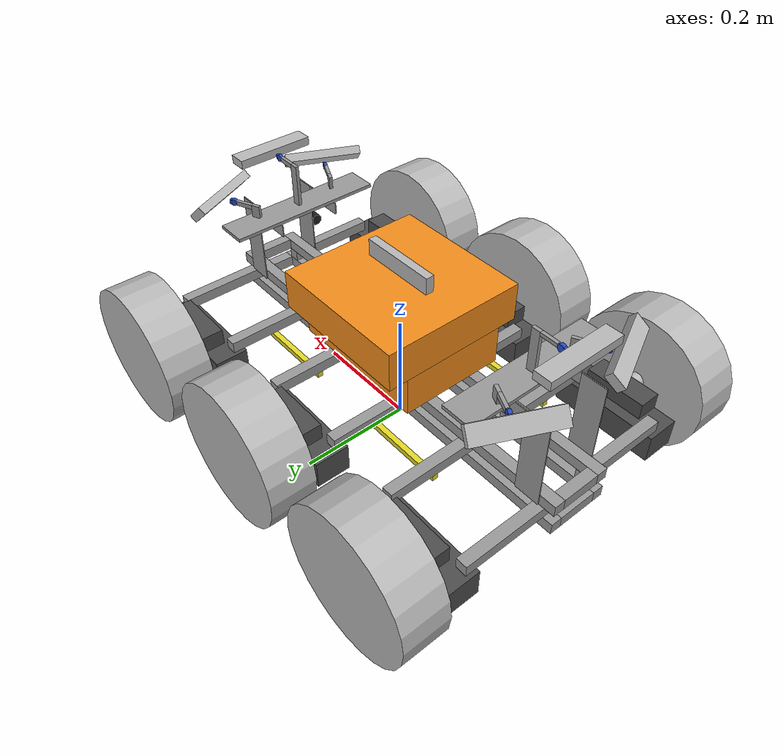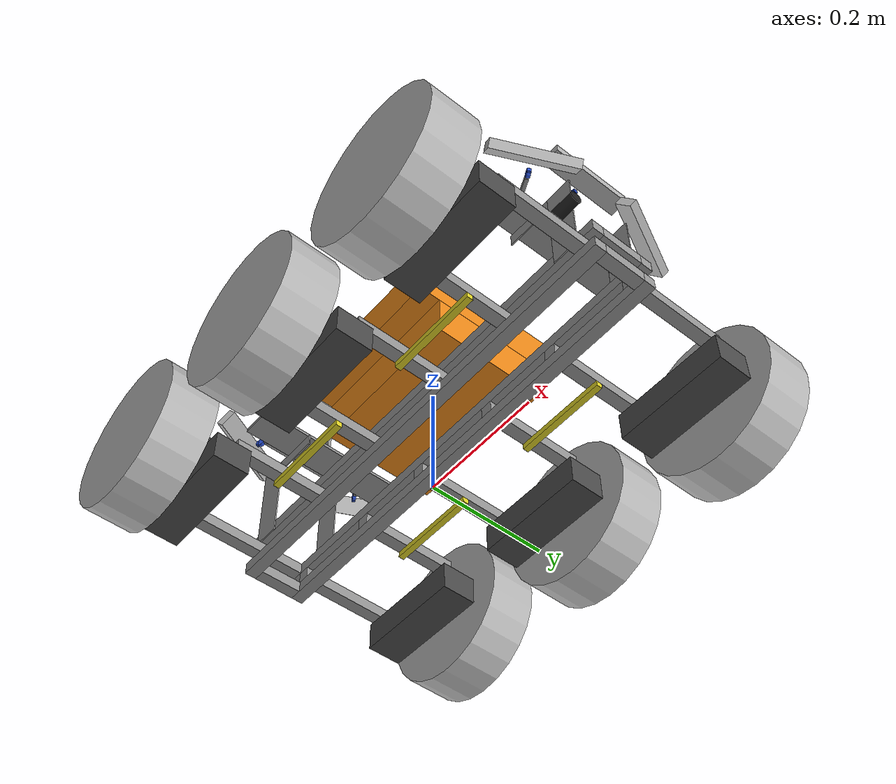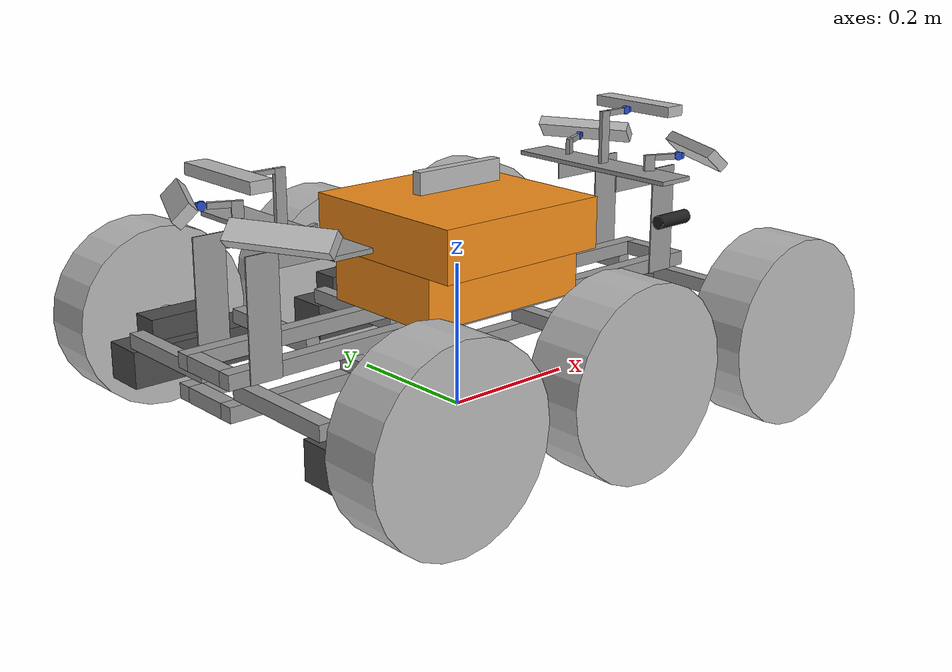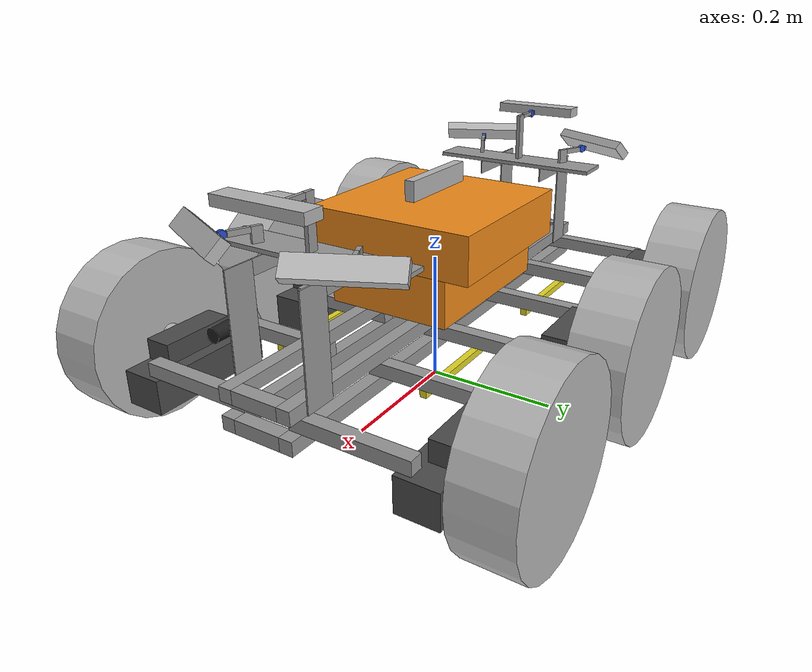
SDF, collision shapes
<?xml version='1.0'?>
 <sdf version='1.5'>
  <model name="siar_model">
   <static>false</static>

 				<!-- DEFINITION OF LINKS -->

<!-- 1. Definition of Chassis-->

    <link name='chassis_1'>
      <pose>0 0.045 .105 0 0 0</pose>
      <inertial>
       <mass>6.0</mass>
       <inertia>
         <ixx>0.0004</ixx>
         <ixy>0.0</ixy>
         <ixz>0.0</ixz>
         <iyy>0.317008</iyy>
         <iyz>0.0</iyz>
         <izz>0.317008</izz>
       </inertia>
      </inertial>
      <collision name='collision'>
        <geometry>
          <box>
            <size>.796 .02 .02</size>
          </box>
        </geometry>
      </collision>
      <visual name='visual'>
        <geometry>
          <box>
            <size>.796 .02 .02</size>
          </box>
        </geometry>
        <material>
          <script>
            <name>Gazebo/Gray</name>
          </script>
        </material>
      </visual>
    </link>

    <link name='chassis_2'>
      <pose>0 -0.045 .105 0 0 0</pose>
      <inertial>
       <mass>6.0</mass>
       <inertia>
         <ixx>0.0004</ixx>
         <ixy>0.0</ixy>
         <ixz>0.0</ixz>
         <iyy>0.317008</iyy>
         <iyz>0.0</iyz>
         <izz>0.317008</izz>
       </inertia>
      </inertial>

      <collision name='collision'>
        <geometry>
          <box>
            <size>.796 .02 .02</size>
          </box>
        </geometry>
      </collision>
      <visual name='visual'>
        <geometry>
          <box>
            <size>.796 .02 .02</size>
          </box>
        </geometry>
        <material>
          <script>
            <name>Gazebo/Gray</name>
          </script>
        </material>
      </visual>
    </link>

    <link name='chassis_3'>
      <pose>0.388 .0 .105 0 0 0</pose>
      <inertial>
       <mass>0.5</mass>
       <inertia>
         <ixx>0.000221</ixx>
         <ixy>0.0</ixy>
         <ixz>0.0</ixz>
         <iyy>0.000033</iyy>
         <iyz>0.0</iyz>
         <izz>0.000221</izz>
       </inertia>
      </inertial>

      <collision name='collision'>
        <geometry>
          <box>
            <size>.02 .07 .02</size>
          </box>
        </geometry>
      </collision>
      <visual name='visual'>
        <geometry>
          <box>
            <size>.02 .07 .02</size>
          </box>
        </geometry>
        <material>
          <script>
            <name>Gazebo/Gray</name>
          </script>
        </material>
      </visual>
    </link>

    <link name='chassis_4'>
      <pose>-0.388 .0 .105 0 0 0</pose>
      <inertial>
       <mass>0.5</mass>
       <inertia>
         <ixx>0.000221</ixx>
         <ixy>0.0</ixy>
         <ixz>0.0</ixz>
         <iyy>0.000033</iyy>
         <iyz>0.0</iyz>
         <izz>0.000221</izz>
       </inertia>
      </inertial>
      <collision name='collision'>
        <geometry>
          <box>
            <size>.02 .07 .02</size>
          </box>
        </geometry>
      </collision>
      <visual name='visual'>
        <geometry>
          <box>
            <size>.02 .07 .02</size>
          </box>
        </geometry>
        <material>
          <script>
            <name>Gazebo/Gray</name>
          </script>
        </material>
      </visual>
    </link>

    <joint type="fixed" name="joint_chassis_1_3">
      <pose>.388 0 0 0 0 0</pose>
      <child>chassis_1</child>
      <parent>chassis_3</parent>
    </joint>
    <joint type="fixed" name="joint_chassis_1_4">
      <pose>-.388 0 0 0 0 0</pose>
      <child>chassis_1</child>
      <parent>chassis_4</parent>
    </joint>
    <joint type="fixed" name="joint_chassis_2_3">
      <pose>.388 0 0 0 0 0</pose>
      <child>chassis_2</child>
      <parent>chassis_3</parent>
    </joint>
    <joint type="fixed" name="joint_chassis_2_4">
      <pose>-.388 0 0 0 0 0</pose>
      <child>chassis_2</child>
      <parent>chassis_4</parent>
    </joint>

<!-- 2. Definition of Arms -->

    <link name='arm_right_1_1'>
      <pose>.078 .12 .125 0 0 0</pose>
      <inertial>
       <mass>1.5</mass>
       <inertia>
         <ixx>0.003663</ixx>
         <ixy>0.0</ixy>
         <ixz>0.0</ixz>
         <iyy>0.0001</iyy>
         <iyz>0.0</iyz>
         <izz>0.003663</izz>
       </inertia>
      </inertial>
      <collision name='collision'>
        <geometry>
          <box>
            <size>.02 .17 .02</size>
          </box>
        </geometry>
      </collision>
      <visual name='visual'>
        <geometry>
          <box>
            <size>.02 .17 .02</size>
          </box>
        </geometry>
        <material>
          <script>
            <name>Gazebo/Gray</name>
          </script>
        </material>
      </visual>
     </link>

    <link name='arm_right_1_2'>
      <pose>-.078 .12 .125 0 0 0</pose>
      <inertial>
       <mass>1.5</mass>
       <inertia>
         <ixx>0.003663</ixx>
         <ixy>0.0</ixy>
         <ixz>0.0</ixz>
         <iyy>0.0001</iyy>
         <iyz>0.0</iyz>
         <izz>0.003663</izz>
       </inertia>
      </inertial>
      <collision name='collision'>
        <geometry>
          <box>
            <size>.02 .17 .02</size>
          </box>
        </geometry>
      </collision>
      <visual name='visual'>
        <geometry>
          <box>
            <size>.02 .17 .02</size>
          </box>
        </geometry>
        <material>
          <script>
            <name>Gazebo/Gray</name>
          </script>
        </material>
      </visual>
     </link>

     <link name='arm_right_2_1'>
      <pose>.214 .12 .125 0 0 0</pose>
      <inertial>
       <mass>1.5</mass>
       <inertia>
         <ixx>0.003663</ixx>
         <ixy>0.0</ixy>
         <ixz>0.0</ixz>
         <iyy>0.0001</iyy>
         <iyz>0.0</iyz>
         <izz>0.003663</izz>
       </inertia>
      </inertial>
      <collision name='collision'>
        <geometry>
          <box>
            <size>.02 .17 .02</size>
          </box>
        </geometry>
      </collision>
      <visual name='visual'>
        <geometry>
          <box>
            <size>.02 .17 .02</size>
          </box>
        </geometry>
        <material>
          <script>
            <name>Gazebo/Gray</name>
          </script>
        </material>
      </visual>
     </link>

     <link name='arm_right_2_2'>
      <pose>.37 .12 .125 0 0 0</pose>
      <inertial>
       <mass>1.5</mass>
       <inertia>
         <ixx>0.003663</ixx>
         <ixy>0.0</ixy>
         <ixz>0.0</ixz>
         <iyy>0.0001</iyy>
         <iyz>0.0</iyz>
         <izz>0.003663</izz>
       </inertia>
      </inertial>
      <collision name='collision'>
        <geometry>
          <box>
            <size>.02 .17 .02</size>
          </box>
        </geometry>
      </collision>
      <visual name='visual'>
        <geometry>
          <box>
            <size>.02 .17 .02</size>
          </box>
        </geometry>
        <material>
          <script>
            <name>Gazebo/Gray</name>
          </script>
        </material>
      </visual>
     </link>

     <link name='arm_right_3_1'>
      <pose>-.214 .12 .125 0 0 0</pose>
      <inertial>
       <mass>1.5</mass>
       <inertia>
         <ixx>0.003663</ixx>
         <ixy>0.0</ixy>
         <ixz>0.0</ixz>
         <iyy>0.0001</iyy>
         <iyz>0.0</iyz>
         <izz>0.003663</izz>
       </inertia>
      </inertial>
      <collision name='collision'>
        <geometry>
          <box>
            <size>.02 .17 .02</size>
          </box>
        </geometry>
      </collision>
      <visual name='visual'>
        <geometry>
          <box>
            <size>.02 .17 .02</size>
          </box>
        </geometry>
        <material>
          <script>
            <name>Gazebo/Gray</name>
          </script>
        </material>
      </visual>
     </link>

     <link name='arm_right_3_2'>
      <pose>-.37 .12 .125 0 0 0</pose>
      <inertial>
       <mass>1.5</mass>
       <inertia>
         <ixx>0.003663</ixx>
         <ixy>0.0</ixy>
         <ixz>0.0</ixz>
         <iyy>0.0001</iyy>
         <iyz>0.0</iyz>
         <izz>0.003663</izz>
       </inertia>
      </inertial>
      <collision name='collision'>
        <geometry>
          <box>
            <size>.02 .17 .02</size>
          </box>
        </geometry>
      </collision>
      <visual name='visual'>
        <geometry>
          <box>
            <size>.02 .17 .02</size>
          </box>
        </geometry>
        <material>
          <script>
            <name>Gazebo/Gray</name>
          </script>
        </material>
      </visual>
    </link>

    <link name='arm_left_1_1'>
       <pose>.078 -.12 .125 0 0 0</pose>
       <inertial>
       <mass>1.5</mass>
       <inertia>
         <ixx>0.003663</ixx>
         <ixy>0.0</ixy>
         <ixz>0.0</ixz>
         <iyy>0.0001</iyy>
         <iyz>0.0</iyz>
         <izz>0.003663</izz>
         </inertia>
       </inertial>
       <collision name='collision'>
        <geometry>
          <box>
            <size>.02 .17 .02</size>
          </box>
        </geometry>
      </collision>
      <visual name='visual'>
        <geometry>
          <box>
            <size>.02 .17 .02</size>
          </box>
        </geometry>
        <material>
          <script>
            <name>Gazebo/Gray</name>
          </script>
        </material>
      </visual>
    </link>

    <link name='arm_left_1_2'>
      <pose>-.078 -.12 .125 0 0 0</pose>
      <inertial>
       <mass>1.5</mass>
       <inertia>
         <ixx>0.003663</ixx>
         <ixy>0.0</ixy>
         <ixz>0.0</ixz>
         <iyy>0.0001</iyy>
         <iyz>0.0</iyz>
         <izz>0.003663</izz>
       </inertia>
      </inertial>
      <collision name='collision'>
        <geometry>
          <box>
            <size>.02 .17 .02</size>
          </box>
        </geometry>
      </collision>
      <visual name='visual'>
        <geometry>
          <box>
            <size>.02 .17 .02</size>
          </box>
        </geometry>
        <material>
          <script>
            <name>Gazebo/Gray</name>
          </script>
        </material>
      </visual>
    </link>

    <link name='arm_left_2_1'>
      <pose>.214 -.12 .125 0 0 0</pose>
      <inertial>
       <mass>1.5</mass>
       <inertia>
         <ixx>0.003663</ixx>
         <ixy>0.0</ixy>
         <ixz>0.0</ixz>
         <iyy>0.0001</iyy>
         <iyz>0.0</iyz>
         <izz>0.003663</izz>
       </inertia>
      </inertial>
      <collision name='collision'>
        <geometry>
          <box>
            <size>.02 .17 .02</size>
          </box>
        </geometry>
      </collision>
      <visual name='visual'>
        <geometry>
          <box>
            <size>.02 .17 .02</size>
          </box>
        </geometry>
        <material>
          <script>
            <name>Gazebo/Gray</name>
          </script>
        </material>
      </visual>
    </link>

  <link name='arm_left_2_2'>
      <pose>.37 -.12 .125 0 0 0</pose>
      <inertial>
       <mass>1.5</mass>
       <inertia>
         <ixx>0.003663</ixx>
         <ixy>0.0</ixy>
         <ixz>0.0</ixz>
         <iyy>0.0001</iyy>
         <iyz>0.0</iyz>
         <izz>0.003663</izz>
       </inertia>
      </inertial>
      <collision name='collision'>
        <geometry>
          <box>
            <size>.02 .17 .02</size>
          </box>
        </geometry>
      </collision>
      <visual name='visual'>
        <geometry>
          <box>
            <size>.02 .17 .02</size>
          </box>
        </geometry>
        <material>
          <script>
            <name>Gazebo/Gray</name>
          </script>
        </material>
      </visual>
   </link>

  <link name='arm_left_3_1'>
      <pose>-.214 -.12 .125 0 0 0</pose>
      <inertial>
       <mass>1.5</mass>
       <inertia>
         <ixx>0.003663</ixx>
         <ixy>0.0</ixy>
         <ixz>0.0</ixz>
         <iyy>0.0001</iyy>
         <iyz>0.0</iyz>
         <izz>0.003663</izz>
       </inertia>
      </inertial>
      <collision name='collision'>
        <geometry>
          <box>
            <size>.02 .17 .02</size>
          </box>
        </geometry>
      </collision>
      <visual name='visual'>
        <geometry>
          <box>
            <size>.02 .17 .02</size>
          </box>
        </geometry>
        <material>
          <script>
            <name>Gazebo/Gray</name>
          </script>
        </material>
      </visual>
   </link>

  <link name='arm_left_3_2'>
      <pose>-.37 -.12 .125 0 0 0</pose>
      <inertial>
       <mass>1.5</mass>
       <inertia>
         <ixx>0.003663</ixx>
         <ixy>0.0</ixy>
         <ixz>0.0</ixz>
         <iyy>0.0001</iyy>
         <iyz>0.0</iyz>
         <izz>0.003663</izz>
       </inertia>
      </inertial>
      <collision name='collision'>
        <geometry>
          <box>
            <size>.02 .17 .02</size>
          </box>
        </geometry>
      </collision>
      <visual name='visual'>
        <geometry>
          <box>
            <size>.02 .17 .02</size>
          </box>
        </geometry>
        <material>
          <script>
            <name>Gazebo/Gray</name>
          </script>
        </material>
      </visual>
    </link>

      <joint type="revolute" name="hinge_arm_right_1_1">
      <pose>0 -.075 -0.01 0 0 0</pose>
      <child>arm_right_1_1</child>
      <parent>chassis_1</parent>
      <axis>
        <limit>
          <lower>-1.2</lower>
          <upper>1.2</upper>
        </limit>
        <xyz>0 0 1</xyz>
        <dynamics>
          <spring_reference>0</spring_reference>
          <spring_stiffness>0</spring_stiffness>
          <damping>0.1</damping>
          <friction>0.5</friction>
        </dynamics>
      </axis>
      </joint>
      <joint type="revolute" name="hinge_arm_right_1_2">
      <pose>0 -.075 -0.01 0 0 0</pose>
      <child>arm_right_1_2</child>
      <parent>chassis_1</parent>
      <axis>
        <limit>
          <lower>-1.2</lower>
          <upper>1.2</upper>
        </limit>
        <xyz>0 0 1</xyz>
        <dynamics>
          <spring_reference>0</spring_reference>
          <spring_stiffness>0</spring_stiffness>
          <damping>0.1</damping>
          <friction>0.5</friction>
        </dynamics>
      </axis>
      </joint>
      <joint type="revolute" name="hinge_arm_right_2_1">
      <pose>0 -.075 -0.01 0 0 0</pose>
      <child>arm_right_2_1</child>
      <parent>chassis_1</parent>
      <axis>
        <limit>
          <lower>-1.2</lower>
          <upper>1.2</upper>
        </limit>
        <xyz>0 0 1</xyz>
        <dynamics>
          <spring_reference>0</spring_reference>
          <spring_stiffness>0</spring_stiffness>
          <damping>0.1</damping>
          <friction>0.5</friction>
        </dynamics>
      </axis>
      </joint>

      <joint type="revolute" name="hinge_arm_right_2_2">
      <pose>0 -.075 -0.01 0 0 0</pose>
      <child>arm_right_2_2</child>
      <parent>chassis_1</parent>
      <axis>
        <limit>
          <lower>-1.2</lower>
          <upper>1.2</upper>
        </limit>
        <xyz>0 0 1</xyz>
        <dynamics>
          <spring_reference>0</spring_reference>
          <spring_stiffness>0</spring_stiffness>
          <damping>0.1</damping>
          <friction>0.5</friction>
        </dynamics>
      </axis>
      </joint>

      <joint type="revolute" name="hinge_arm_right_3_1">
      <pose>0 -.075 -0.01 0 0 0</pose>
      <child>arm_right_3_1</child>
      <parent>chassis_1</parent>
      <axis>
        <limit>
          <lower>-1.2</lower>
          <upper>1.2</upper>
        </limit>
        <xyz>0 0 1</xyz>
        <dynamics>
          <spring_reference>0</spring_reference>
          <spring_stiffness>0</spring_stiffness>
          <damping>0.1</damping>
          <friction>0.5</friction>
        </dynamics>
      </axis>
      </joint>
      <joint type="revolute" name="hinge_arm_right_3_2">
      <pose>0 -.075 -0.01 0 0 0</pose>
      <child>arm_right_3_2</child>
      <parent>chassis_1</parent>
      <axis>
        <limit>
          <lower>-1.2</lower>
          <upper>1.2</upper>
        </limit>
        <xyz>0 0 1</xyz>
        <dynamics>
          <spring_reference>0</spring_reference>
          <spring_stiffness>0</spring_stiffness>
          <damping>0.1</damping>
          <friction>0.5</friction>
        </dynamics>
      </axis>
      </joint>
      <joint type="revolute" name="hinge_arm_left_1_1">
      <pose>0 .075 -0.01 0 0 0</pose>
      <child>arm_left_1_1</child>
      <parent>chassis_2</parent>
      <axis>
        <limit>
          <lower>-1.2</lower>
          <upper>1.2</upper>
        </limit>
        <xyz>0 0 1</xyz>
        <dynamics>
          <spring_reference>0</spring_reference>
          <spring_stiffness>0</spring_stiffness>
          <damping>0.1</damping>
          <friction>0.5</friction>
        </dynamics>
      </axis>
      </joint>
      <joint type="revolute" name="hinge_arm_left_1_2">
      <pose>0 .075 -0.01 0 0 0</pose>
      <child>arm_left_1_2</child>
      <parent>chassis_2</parent>
      <axis>
        <limit>
          <lower>-1.2</lower>
          <upper>1.2</upper>
        </limit>
        <xyz>0 0 1</xyz>
        <dynamics>
          <spring_reference>0</spring_reference>
          <spring_stiffness>0</spring_stiffness>
          <damping>0.1</damping>
          <friction>0.5</friction>
        </dynamics>
      </axis>
      </joint>
      <joint type="revolute" name="hinge_arm_left_2_1">
      <pose>0 .075 -0.01 0 0 0</pose>
      <child>arm_left_2_1</child>
      <parent>chassis_2</parent>
      <axis>
        <limit>
          <lower>-1.2</lower>
          <upper>1.2</upper>
        </limit>
        <xyz>0 0 1</xyz>
        <dynamics>
          <spring_reference>0</spring_reference>
          <spring_stiffness>0</spring_stiffness>
          <damping>0.1</damping>
          <friction>0.5</friction>
        </dynamics>
      </axis>
      </joint>
      <joint type="revolute" name="hinge_arm_left_2_2">
      <pose>0 .075 -0.01 0 0 0</pose>
      <child>arm_left_2_2</child>
      <parent>chassis_2</parent>
      <axis>
        <limit>
          <lower>-1.2</lower>
          <upper>1.2</upper>
        </limit>
        <xyz>0 0 1</xyz>
        <dynamics>
          <spring_reference>0</spring_reference>
          <spring_stiffness>0</spring_stiffness>
          <damping>0.1</damping>
          <friction>0.5</friction>
        </dynamics>
      </axis>
      </joint>
      <joint type="revolute" name="hinge_arm_left_3_1">
      <pose>0 .075 -0.01 0 0 0</pose>
      <child>arm_left_3_1</child>
      <parent>chassis_2</parent>
      <axis>
        <limit>
          <lower>-1.2</lower>
          <upper>1.2</upper>
        </limit>
        <xyz>0 0 1</xyz>
        <dynamics>
          <spring_reference>0</spring_reference>
          <spring_stiffness>0</spring_stiffness>
          <damping>0.1</damping>
          <friction>0.5</friction>
        </dynamics>
      </axis>
      </joint>
      <joint type="revolute" name="hinge_arm_left_3_2">
      <pose>0 .075 -0.01 0 0 0</pose>
      <child>arm_left_3_2</child>
      <parent>chassis_2</parent>
      <axis>
        <limit>
          <lower>-1.2</lower>
          <upper>1.2</upper>
        </limit>
        <xyz>0 0 1</xyz>
        <dynamics>
          <spring_reference>0</spring_reference>
          <spring_stiffness>0</spring_stiffness>
          <damping>0.1</damping>
          <friction>0.5</friction>
        </dynamics>
      </axis>
      </joint>

<!-- 3. Definition of Upper Chassis -->

    <link name='chassis_5'>
      <pose>0 0.045 .145 0 0 0</pose>
      <inertial>
       <mass>6.0</mass>
       <inertia>
         <ixx>0.0004</ixx>
         <ixy>0.0</ixy>
         <ixz>0.0</ixz>
         <iyy>0.317008</iyy>
         <iyz>0.0</iyz>
         <izz>0.317008</izz>
       </inertia>
      </inertial>
      <collision name='collision'>
        <geometry>
          <box>
            <size>.796 .02 .02</size>
          </box>
        </geometry>
      </collision>
      <visual name='visual'>
        <geometry>
          <box>
            <size>.796 .02 .02</size>
          </box>
        </geometry>
        <material>
          <script>
            <name>Gazebo/Gray</name>
          </script>
        </material>
      </visual>
    </link>

    <link name='chassis_6'>
      <pose>0 -0.045 .145 0 0 0</pose>
      <inertial>
       <mass>6.0</mass>
       <inertia>
         <ixx>0.0004</ixx>
         <ixy>0.0</ixy>
         <ixz>0.0</ixz>
         <iyy>0.317008</iyy>
         <iyz>0.0</iyz>
         <izz>0.317008</izz>
       </inertia>
      </inertial>
      <collision name='collision'>
        <geometry>
          <box>
            <size>.796 .02 .02</size>
          </box>
        </geometry>
      </collision>
      <visual name='visual'>
        <geometry>
          <box>
            <size>.796 .02 .02</size>
          </box>
        </geometry>
        <material>
          <script>
            <name>Gazebo/Gray</name>
          </script>
        </material>
      </visual>
    </link>

    <link name='chassis_7'>
      <pose>0.388 .0 .145 0 0 0</pose>
      <inertial>
       <mass>0.5</mass>
       <inertia>
         <ixx>0.000221</ixx>
         <ixy>0.0</ixy>
         <ixz>0.0</ixz>
         <iyy>0.000033</iyy>
         <iyz>0.0</iyz>
         <izz>0.000221</izz>
       </inertia>
      </inertial>

      <collision name='collision'>
        <geometry>
          <box>
            <size>.02 .07 .02</size>
          </box>
        </geometry>
      </collision>
      <visual name='visual'>
        <geometry>
          <box>
            <size>.02 .07 .02</size>
          </box>
        </geometry>
        <material>
          <script>
            <name>Gazebo/Gray</name>
          </script>
        </material>
      </visual>
    </link>

    <link name='chassis_8'>
      <pose>-0.388 .0 .145 0 0 0</pose>
      <inertial>
       <mass>0.5</mass>
       <inertia>
         <ixx>0.000221</ixx>
         <ixy>0.0</ixy>
         <ixz>0.0</ixz>
         <iyy>0.000033</iyy>
         <iyz>0.0</iyz>
         <izz>0.000221</izz>
       </inertia>
      </inertial>
      <collision name='collision'>
        <geometry>
          <box>
            <size>.02 .07 .02</size>
          </box>
        </geometry>
      </collision>
      <visual name='visual'>
        <geometry>
          <box>
            <size>.02 .07 .02</size>
          </box>
        </geometry>
        <material>
          <script>
            <name>Gazebo/Gray</name>
          </script>
        </material>
      </visual>
    </link>

    <joint type="fixed" name="joint_chassis_5_7">
      <pose>.388 0 0 0 0 0</pose>
      <child>chassis_5</child>
      <parent>chassis_7</parent>
    </joint>
    <joint type="fixed" name="joint_chassis_5_8">
      <pose>-.388 0 0 0 0 0</pose>
      <child>chassis_5</child>
      <parent>chassis_8</parent>
    </joint>
    <joint type="fixed" name="joint_chassis_6_7">
      <pose>.388 0 0 0 0 0</pose>
      <child>chassis_6</child>
      <parent>chassis_7</parent>
    </joint>
    <joint type="fixed" name="joint_chassis_6_8">
      <pose>-.388 0 0 0 0 0</pose>
      <child>chassis_6</child>
      <parent>chassis_8</parent>
    </joint>

      <joint type="revolute" name="upch_arm_right_1_1">
      <pose>0 -.075 0.01 0 0 0</pose>
      <child>arm_right_1_1</child>
      <parent>chassis_5</parent>
      <axis>
        <limit>
          <lower>-1.2</lower>
          <upper>1.2</upper>
        </limit>
        <xyz>0 0 1</xyz>
        <dynamics>
          <spring_reference>0</spring_reference>
          <spring_stiffness>0</spring_stiffness>
          <damping>0.1</damping>
          <friction>0.5</friction>
        </dynamics>
      </axis>
      </joint>
      <joint type="revolute" name="upch_arm_right_1_2">
      <pose>0 -.075 0.01 0 0 0</pose>
      <child>arm_right_1_2</child>
      <parent>chassis_5</parent>
      <axis>
        <limit>
          <lower>-1.2</lower>
          <upper>1.2</upper>
        </limit>
        <xyz>0 0 1</xyz>
        <dynamics>
          <spring_reference>0</spring_reference>
          <spring_stiffness>0</spring_stiffness>
          <damping>0.1</damping>
          <friction>0.5</friction>
        </dynamics>
      </axis>
      </joint>
      <joint type="revolute" name="upch_arm_right_2_1">
      <pose>0 -.075 0.01 0 0 0</pose>
      <child>arm_right_2_1</child>
      <parent>chassis_5</parent>
      <axis>
        <limit>
          <lower>-1.2</lower>
          <upper>1.2</upper>
        </limit>
        <xyz>0 0 1</xyz>
        <dynamics>
          <spring_reference>0</spring_reference>
          <spring_stiffness>0</spring_stiffness>
          <damping>0.1</damping>
          <friction>0.5</friction>
        </dynamics>
      </axis>
      </joint>

      <joint type="revolute" name="upch_arm_right_2_2">
      <pose>0 -.075 0.01 0 0 0</pose>
      <child>arm_right_2_2</child>
      <parent>chassis_5</parent>
      <axis>
        <limit>
          <lower>-1.2</lower>
          <upper>1.2</upper>
        </limit>
        <xyz>0 0 1</xyz>
        <dynamics>
          <spring_reference>0</spring_reference>
          <spring_stiffness>0</spring_stiffness>
          <damping>0.1</damping>
          <friction>0.5</friction>
        </dynamics>
      </axis>
      </joint>

      <joint type="revolute" name="upch_arm_right_3_1">
      <pose>0 -.075 0.01 0 0 0</pose>
      <child>arm_right_3_1</child>
      <parent>chassis_5</parent>
      <axis>
        <limit>
          <lower>-1.2</lower>
          <upper>1.2</upper>
        </limit>
        <xyz>0 0 1</xyz>
        <dynamics>
          <spring_reference>0</spring_reference>
          <spring_stiffness>0</spring_stiffness>
          <damping>0.1</damping>
          <friction>0.5</friction>
        </dynamics>
      </axis>
      </joint>
      <joint type="revolute" name="upch_arm_right_3_2">
      <pose>0 -.075 0.01 0 0 0</pose>
      <child>arm_right_3_2</child>
      <parent>chassis_5</parent>
      <axis>
        <limit>
          <lower>-1.2</lower>
          <upper>1.2</upper>
        </limit>
        <xyz>0 0 1</xyz>
        <dynamics>
          <spring_reference>0</spring_reference>
          <spring_stiffness>0</spring_stiffness>
          <damping>0.1</damping>
          <friction>0.5</friction>
        </dynamics>
      </axis>
      </joint>
      <joint type="revolute" name="upch_arm_left_1_1">
      <pose>0 .075 0.01 0 0 0</pose>
      <child>arm_left_1_1</child>
      <parent>chassis_6</parent>
      <axis>
        <limit>
          <lower>-1.2</lower>
          <upper>1.2</upper>
        </limit>
        <xyz>0 0 1</xyz>
        <dynamics>
          <spring_reference>0</spring_reference>
          <spring_stiffness>0</spring_stiffness>
          <damping>0.1</damping>
          <friction>0.5</friction>
        </dynamics>
      </axis>
      </joint>
      <joint type="revolute" name="upch_arm_left_1_2">
      <pose>0 .075 0.01 0 0 0</pose>
      <child>arm_left_1_2</child>
      <parent>chassis_6</parent>
      <axis>
        <limit>
          <lower>-1.2</lower>
          <upper>1.2</upper>
        </limit>
        <xyz>0 0 1</xyz>
        <dynamics>
          <spring_reference>0</spring_reference>
          <spring_stiffness>0</spring_stiffness>
          <damping>0.1</damping>
          <friction>0.5</friction>
        </dynamics>
      </axis>
      </joint>
      <joint type="revolute" name="upch_arm_left_2_1">
      <pose>0 .075 0.01 0 0 0</pose>
      <child>arm_left_2_1</child>
      <parent>chassis_6</parent>
      <axis>
        <limit>
          <lower>-1.2</lower>
          <upper>1.2</upper>
        </limit>
        <xyz>0 0 1</xyz>
        <dynamics>
          <spring_reference>0</spring_reference>
          <spring_stiffness>0</spring_stiffness>
          <damping>0.1</damping>
          <friction>0.5</friction>
        </dynamics>
      </axis>
      </joint>
      <joint type="revolute" name="upch_arm_left_2_2">
      <pose>0 .075 0.01 0 0 0</pose>
      <child>arm_left_2_2</child>
      <parent>chassis_6</parent>
      <axis>
        <limit>
          <lower>-1.2</lower>
          <upper>1.2</upper>
        </limit>
        <xyz>0 0 1</xyz>
        <dynamics>
          <spring_reference>0</spring_reference>
          <spring_stiffness>0</spring_stiffness>
          <damping>0.1</damping>
          <friction>0.5</friction>
        </dynamics>
      </axis>
      </joint>
      <joint type="revolute" name="upch_arm_left_3_1">
      <pose>0 .075 0.01 0 0 0</pose>
      <child>arm_left_3_1</child>
      <parent>chassis_6</parent>
      <axis>
        <limit>
          <lower>-1.2</lower>
          <upper>1.2</upper>
        </limit>
        <xyz>0 0 1</xyz>
        <dynamics>
          <spring_reference>0</spring_reference>
          <spring_stiffness>0</spring_stiffness>
          <damping>0.1</damping>
          <friction>0.5</friction>
        </dynamics>
      </axis>
      </joint>
      <joint type="revolute" name="upch_arm_left_3_2">
      <pose>0 .075 0.01 0 0 0</pose>
      <child>arm_left_3_2</child>
      <parent>chassis_6</parent>
      <axis>
        <limit>
          <lower>-1.2</lower>
          <upper>1.2</upper>
        </limit>
        <xyz>0 0 1</xyz>
        <dynamics>
          <spring_reference>0</spring_reference>
          <spring_stiffness>0</spring_stiffness>
          <damping>0.1</damping>
          <friction>0.5</friction>
        </dynamics>
      </axis>
      </joint>

<!-- 4. Box of battery and electronic and Handle to Cameras  -->

   <link name="box_battery">
      <inertial>
       <pose>.0 .0 .225 0 0 0</pose>
       <mass>14</mass>
       <inertia>
         <ixx>0.064983</ixx>
         <ixy>0.0</ixy>
         <ixz>0.0</ixz>
         <iyy>0.101733</iyy>
         <iyz>0.0</iyz>
         <izz>0.120983</izz>
       </inertia>
      </inertial>
      <collision name='collision_1'>
      <pose>.0 .0 .26 0 0 0</pose>
        <geometry>
          <box>
            <size>.26 .26 .07</size>
          </box>
        </geometry>
      </collision>
      <visual name='visual_1'>
      <pose>.0 .0 .26 0 0 0</pose>
        <geometry>
          <box>
            <size>.26 .26 .07</size>
          </box>
        </geometry>
        <material>
          <script>
            <name>Gazebo/Orange</name>
          </script>
        </material>
      </visual>
      <collision name='collision_2'>
      <pose>.0 .0 .19 0 0 0</pose>
        <geometry>
          <box>
            <size>.26 .19 .07</size>
          </box>
        </geometry>
      </collision>
      <visual name='visual_2'>
      <pose>.0 .0 .19 0 0 0</pose>
        <geometry>
          <box>
            <size>.26 .19 .07</size>
          </box>
        </geometry>
        <material>
          <script>
            <name>Gazebo/Orange</name>
          </script>
        </material>
      </visual>
      <visual name='visual_3'>
      <pose>.0 .0 .2975 0 0 0</pose>
        <geometry>
          <box>
            <size>.30 .30 .005</size>
          </box>
        </geometry>
        <material>
          <script>
            <name>Gazebo/Black</name>
          </script>
        </material>
      </visual>
      <visual name='visual_4'>
      <pose>.0 .0 .3005 0 0 0</pose>
        <geometry>
          <box>
            <size>.28 .28 .001</size>
          </box>
        </geometry>
        <material>
          <script>
            <name>Gazebo/DarkGrey</name>
          </script>
        </material>
      </visual>
      <sensor name="imu_sensor" type="imu">
	<always_on>true</always_on>
	<update_rate>100</update_rate>
	<visualize>true</visualize>
	<topic>imu_siar_topic</topic>
	<plugin filename="libgazebo_ros_imu_sensor.so" name="imu_plugin">
	  <topicName>imu</topicName>
	  <bodyName>imu_link</bodyName>
	  <updateRateHZ>10.0</updateRateHZ>
	  <gaussianNoise>0.0</gaussianNoise>
	  <xyzOffset>0 0 0</xyzOffset>
	  <rpyOffset>0 0 0</rpyOffset>
	  <frameName>imu_link</frameName>
	</plugin>
	<pose>0 0 0 0 0 0</pose>
      </sensor>
   </link>

    <joint type="fixed" name="joint_box_1">
      <pose>0 0 0 0 0 0</pose>
      <child>chassis_5</child>
      <parent>box_battery</parent>
    </joint>
    <joint type="fixed" name="joint_box_2">
      <pose>0 0 0 0 0 0</pose>
      <child>chassis_6</child>
      <parent>box_battery</parent>
    </joint>

   <link name="handle_camera_front_1">
      <pose>.3465 .056 .213 0 0 0</pose>
      <inertial>
       <mass>1.5</mass>
       <inertia>
         <ixx>0.003046</ixx>
         <ixy>0.0</ixy>
         <ixz>0.0</ixz>
         <iyy>0.003295</iyy>
         <iyz>0.0</iyz>
         <izz>0.000254</izz>
       </inertia>
      </inertial>
      <collision name='collision_1'>
        <geometry>
          <box>
            <size>.045 .002 .156</size>
          </box>
        </geometry>
      </collision>
      <visual name='visual_1'>
        <geometry>
          <box>
            <size>.045 .002 .156 </size>
          </box>
        </geometry>
        <material>
          <script>
            <name>Gazebo/Gray</name>
          </script>
        </material>
      </visual>
   </link>

   <link name="handle_camera_front_1_1">
      <pose>.285 .056 .28 0 0 0</pose>
      <inertial>
       <mass>1.5</mass>
       <inertia>
         <ixx>0.000061</ixx>
         <ixy>0.0</ixy>
         <ixz>0.0</ixz>
         <iyy>0.000821</iyy>
         <iyz>0.0</iyz>
         <izz>0.000761</izz>
       </inertia>
      </inertial>
      <collision name='collision_1'>
        <geometry>
          <box>
            <size>.078 .002 .022</size>
          </box>
        </geometry>
      </collision>
      <visual name='visual_1'>
        <geometry>
          <box>
            <size>.078 .002 .022 </size>
          </box>
        </geometry>
        <material>
          <script>
            <name>Gazebo/Gray</name>
          </script>
        </material>
      </visual>
   </link>

   <link name="handle_camera_front_2">
      <pose>.3465 -.056 .213 0 0 0</pose>
      <inertial>
       <mass>1.5</mass>
       <inertia>
         <ixx>0.003046</ixx>
         <ixy>0.0</ixy>
         <ixz>0.0</ixz>
         <iyy>0.003295</iyy>
         <iyz>0.0</iyz>
         <izz>0.000254</izz>
       </inertia>
      </inertial>
      <collision name='collision_1'>
        <geometry>
          <box>
            <size>.045 .002 .156</size>
          </box>
        </geometry>
      </collision>
      <visual name='visual_1'>
        <geometry>
          <box>
            <size>.045 .002 .156 </size>
          </box>
        </geometry>
        <material>
          <script>
            <name>Gazebo/Gray</name>
          </script>
        </material>
      </visual>
   </link>

   <link name="handle_camera_front_2_1">
      <pose>.285 -.056 .28 0 0 0</pose>
      <inertial>
       <mass>1.5</mass>
       <inertia>
         <ixx>0.000061</ixx>
         <ixy>0.0</ixy>
         <ixz>0.0</ixz>
         <iyy>0.000821</iyy>
         <iyz>0.0</iyz>
         <izz>0.000761</izz>
       </inertia>
      </inertial>
      <collision name='collision_1'>
        <geometry>
          <box>
            <size>.078 .002 .022</size>
          </box>
        </geometry>
      </collision>
      <visual name='visual_1'>
        <geometry>
          <box>
            <size>.078 .002 .022 </size>
          </box>
        </geometry>
        <material>
          <script>
            <name>Gazebo/Gray</name>
          </script>
        </material>
      </visual>
   </link>

   <joint type="fixed" name="joint_handle_camera_front_1">
     <pose>0 0 -0.078 0 0 0</pose>
     <child>handle_camera_front_1</child>
     <parent>chassis_6</parent>
   </joint>

   <joint type="fixed" name="joint_handle_camera_front_1_1">
     <pose>0.039 0 0 0 0 0</pose>
     <parent>handle_camera_front_1</parent>
     <child>handle_camera_front_1_1</child>
   </joint>

   <joint type="fixed" name="joint_handle_camera_front_2">
     <pose>0 0 -0.078 0 0 0</pose>
     <child>handle_camera_front_2</child>
     <parent>chassis_6</parent>
   </joint>

   <joint type="fixed" name="joint_handle_camera_front_2_1">
     <pose>0.039 0 0 0 0 0</pose>
     <parent>handle_camera_front_2</parent>
     <child>handle_camera_front_2_1</child>
   </joint>

   <link name="handle_camera_back_1">
      <pose>-.3465 .056 .213 0 0 0</pose>
      <inertial>
       <mass>1.5</mass>
       <inertia>
         <ixx>0.003046</ixx>
         <ixy>0.0</ixy>
         <ixz>0.0</ixz>
         <iyy>0.003295</iyy>
         <iyz>0.0</iyz>
         <izz>0.000254</izz>
       </inertia>
      </inertial>
      <collision name='collision_1'>
        <geometry>
          <box>
            <size>.045 .002 .156</size>
          </box>
        </geometry>
      </collision>
      <visual name='visual_1'>
        <geometry>
          <box>
            <size>.045 .002 .156 </size>
          </box>
        </geometry>
        <material>
          <script>
            <name>Gazebo/Gray</name>
          </script>
        </material>
      </visual>
    </link>

    <link name="handle_camera_back_1_1">
      <pose>-.285 .056 .28 0 0 0</pose>
      <inertial>
       <mass>1.5</mass>
       <inertia>
         <ixx>0.000061</ixx>
         <ixy>0.0</ixy>
         <ixz>0.0</ixz>
         <iyy>0.000821</iyy>
         <iyz>0.0</iyz>
         <izz>0.000761</izz>
       </inertia>
      </inertial>
      <collision name='collision_1'>
        <geometry>
          <box>
            <size>.078 .002 .022</size>
          </box>
        </geometry>
      </collision>
      <visual name='visual_1'>
        <geometry>
          <box>
            <size>.078 .002 .022 </size>
          </box>
        </geometry>
        <material>
          <script>
            <name>Gazebo/Gray</name>
          </script>
        </material>
      </visual>
   </link>

   <link name="handle_camera_back_2">
      <pose>-.3465 -.056 .213 0 0 0</pose>
      <inertial>
       <mass>1.5</mass>
       <inertia>
         <ixx>0.003046</ixx>
         <ixy>0.0</ixy>
         <ixz>0.0</ixz>
         <iyy>0.003295</iyy>
         <iyz>0.0</iyz>
         <izz>0.000254</izz>
       </inertia>
      </inertial>
      <collision name='collision_1'>
        <geometry>
          <box>
            <size>.045 .002 .156</size>
          </box>
        </geometry>
      </collision>
      <visual name='visual_1'>
        <geometry>
          <box>
            <size>.045 .002 .156 </size>
          </box>
        </geometry>
        <material>
          <script>
            <name>Gazebo/Gray</name>
          </script>
        </material>
      </visual>
   </link>

   <link name="handle_camera_back_2_1">
      <pose>-.285 -.056 .28 0 0 0</pose>
      <inertial>
       <mass>1.5</mass>
       <inertia>
         <ixx>0.000061</ixx>
         <ixy>0.0</ixy>
         <ixz>0.0</ixz>
         <iyy>0.000821</iyy>
         <iyz>0.0</iyz>
         <izz>0.000761</izz>
       </inertia>
      </inertial>
      <collision name='collision_2'>
        <geometry>
          <box>
            <size>.078 .002 .022</size>
          </box>
        </geometry>
      </collision>
      <visual name='visual_2'>
        <geometry>
          <box>
            <size>.078 .002 .022 </size>
          </box>
        </geometry>
        <material>
          <script>
            <name>Gazebo/Gray</name>
          </script>
        </material>
      </visual>
   </link>

   <joint type="fixed" name="joint_handle_camera_back_1">
     <pose>0 0 -0.078 0 0 0</pose>
     <child>handle_camera_back_1</child>
     <parent>chassis_5</parent>
   </joint>

   <joint type="fixed" name="joint_handle_camera_back_1_1">
     <pose>-0.039 0 0 0 0 0</pose>
     <parent>handle_camera_back_1</parent>
     <child>handle_camera_back_1_1</child>
   </joint>

   <joint type="fixed" name="joint_handle_camera_back_2">
     <pose>0 0 -0.078 0 0 0</pose>
     <child>handle_camera_back_2</child>
     <parent>chassis_5</parent>
   </joint>

   <joint type="fixed" name="joint_handle_camera_back_2_1">
     <pose>-0.039 0 0 0 0 0</pose>
     <parent>handle_camera_back_2</parent>
     <child>handle_camera_back_2_1</child>
   </joint>

   <link name="handle_camera_front_3">
      <pose>.2775 .0 .294 0 0 0</pose>
      <inertial>
       <mass>1</mass>
       <inertia>
         <ixx>0.006443</ixx>
         <ixy>0.0</ixy>
         <ixz>0.0</ixz>
         <iyy>0.000255</iyy>
         <iyz>0.0</iyz>
         <izz>0.006692</izz>
       </inertia>
      </inertial>
      <collision name='collision'>
        <geometry>
          <box>
            <size>.055 .278 .006 </size>
          </box>
        </geometry>
      </collision>
      <visual name='visual'>
        <geometry>
          <box>
            <size>.055 .278 .006 </size>
          </box>
        </geometry>
        <material>
          <script>
            <name>Gazebo/Gray</name>
          </script>
        </material>
      </visual>
   </link>

   <link name="handle_camera_back_3">
      <pose>-.2775 .0 .294 0 0 0</pose>
      <inertial>
       <mass>1</mass>
       <inertia>
         <ixx>0.006443</ixx>
         <ixy>0.0</ixy>
         <ixz>0.0</ixz>
         <iyy>0.000255</iyy>
         <iyz>0.0</iyz>
         <izz>0.006692</izz>
       </inertia>
      </inertial>
      <collision name='collision'>
        <geometry>
          <box>
            <size>.055 .278 .006 </size>
          </box>
        </geometry>
      </collision>
      <visual name='visual'>
        <geometry>
          <box>
            <size>.055 .278 .006 </size>
          </box>
        </geometry>
        <material>
          <script>
            <name>Gazebo/Gray</name>
          </script>
        </material>
      </visual>
   </link>

    <joint type="fixed" name="joint_handle_camera_front_3_1">
      <pose>0 0.056 -0.001 0 0 0</pose>
      <child>handle_camera_front_3</child>
      <parent>handle_camera_front_1_1</parent>
    </joint>

    <joint type="fixed" name="joint_handle_camera_front_3_2">
      <pose>0 -0.056 -0.001 0 0 0</pose>
      <child>handle_camera_front_3</child>
      <parent>handle_camera_front_2_1</parent>
    </joint>

    <joint type="fixed" name="joint_handle_camera_back_3_1">
      <pose>0 0.056 -0.001 0 0 0</pose>
      <child>handle_camera_back_3</child>
      <parent>handle_camera_back_1_1</parent>
    </joint>

    <joint type="fixed" name="joint_handle_camera_back_3_2">
      <pose>0 -0.056 -0.001 0 0 0</pose>
      <child>handle_camera_back_3</child>
      <parent>handle_camera_back_2_1</parent>
    </joint>

   <link name="handle_camera_front_4_1">
      <pose>.28 .0 .3345 0 0 0</pose>
      <inertial>
       <mass>1</mass>
       <inertia>
         <ixx>0.000471</ixx>
         <ixy>0.0</ixy>
         <ixz>0.0</ixz>
         <iyy>0.000488</iyy>
         <iyz>0.0</iyz>
         <izz>0.000022</izz>
       </inertia>
      </inertial>
      <collision name="collision_1">
        <geometry>
          <box>
            <size>.015 .006 .075 </size>
          </box>
        </geometry>
      </collision>
      <visual name="visual_1">
        <geometry>
          <box>
            <size>.015 .006 .075 </size>
          </box>
        </geometry>
        <material>
          <script>
            <name>Gazebo/Gray</name>
          </script>
        </material>
      </visual>
   </link>

   <link name="handle_camera_front_4_1_1">
      <pose>.3025 .0 .368 0 0 0</pose>
      <inertial>
       <mass>1</mass>
       <inertia>
         <ixx>0.000008</ixx>
         <ixy>0.0</ixy>
         <ixz>0.0</ixz>
         <iyy>0.000080</iyy>
         <iyz>0.0</iyz>
         <izz>0.000078</izz>
       </inertia>
      </inertial>
      <collision name="collision_2">
        <geometry>
          <box>
            <size>.03 .006 .008 </size>
          </box>
        </geometry>
      </collision>
      <visual name="visual_2">
        <geometry>
          <box>
            <size>.03 .006 .008 </size>
          </box>
        </geometry>
        <material>
          <script>
            <name>Gazebo/Gray</name>
          </script>
        </material>
      </visual>
   </link>

   <joint type="fixed" name="joint_handle_camera_front_4_1">
     <pose>0 0 -.0375 0 0 0</pose>
     <child>handle_camera_front_4_1</child>
     <parent>handle_camera_front_3</parent>
   </joint>
   <joint type="fixed" name="joint_handle_camera_front_4_1_1">
     <pose>-0.015 0 0 0 0 0</pose>
     <child>handle_camera_front_4_1_1</child>
     <parent>handle_camera_front_4_1</parent>
   </joint>

   <link name="handle_camera_front_4_2">
      <pose>.29 .078 .3082 0 0 0.436332</pose>
      <inertial>
       <mass>1</mass>
       <inertia>
         <ixx>0.000045</ixx>
         <ixy>0.0</ixy>
         <ixz>0.0</ixz>
         <iyy>0.000061</iyy>
         <iyz>0.0</iyz>
         <izz>0.000022</izz>
       </inertia>
      </inertial>
      <collision name="collision_1">
        <geometry>
          <box>
            <size>.015 .006 .0224 </size>
          </box>
        </geometry>
      </collision>
      <visual name="visual_1">
        <geometry>
          <box>
            <size>.015 .006 .0224 </size>
          </box>
        </geometry>
        <material>
          <script>
            <name>Gazebo/Gray</name>
          </script>
        </material>
      </visual>
    </link>

    <link name="handle_camera_front_4_2_1">
      <pose>.3103 .0875 .3154 0 0 0.436332</pose>
      <inertial>
       <mass>1</mass>
       <inertia>
         <ixx>0.000008</ixx>
         <ixy>0.0</ixy>
         <ixz>0.0</ixz>
         <iyy>0.000080</iyy>
         <iyz>0.0</iyz>
         <izz>0.000078</izz>
       </inertia>
      </inertial>
      <collision name="collision_2">
        <geometry>
          <box>
            <size>.03 .006 .008 </size>
          </box>
        </geometry>
      </collision>
      <visual name="visual_2">
        <geometry>
          <box>
            <size>.03 .006 .008 </size>
          </box>
        </geometry>
        <material>
          <script>
            <name>Gazebo/Gray</name>
          </script>
        </material>
      </visual>
   </link>

   <joint type="fixed" name="joint_handle_camera_front_4_2">
     <pose>0 0 -.0112 0 0 0</pose>
     <child>handle_camera_front_4_2</child>
     <parent>handle_camera_front_3</parent>
   </joint>
   <joint type="fixed" name="joint_handle_camera_front_4_2_1">
     <pose>-0.015 0 0 0 0 0</pose>
     <child>handle_camera_front_4_2_1</child>
     <parent>handle_camera_front_4_2</parent>
   </joint>

   <link name="handle_camera_front_4_3">
      <pose>.29 -.078 .3082 0 0 -0.436332</pose>
      <inertial>
       <mass>1</mass>
       <inertia>
         <ixx>0.000045</ixx>
         <ixy>0.0</ixy>
         <ixz>0.0</ixz>
         <iyy>0.000061</iyy>
         <iyz>0.0</iyz>
         <izz>0.000022</izz>
       </inertia>
      </inertial>
      <collision name="collision_1">
        <geometry>
          <box>
            <size>.015 .006 .0224 </size>
          </box>
        </geometry>
      </collision>
      <visual name="visual_1">
        <geometry>
          <box>
            <size>.015 .006 .0224 </size>
          </box>
        </geometry>
        <material>
          <script>
            <name>Gazebo/Gray</name>
          </script>
        </material>
      </visual>
   </link>

   <link name="handle_camera_front_4_3_1">
      <pose>.3103 -.0875 .3154 0 0 -0.436332</pose>
      <inertial>
       <mass>1</mass>
       <inertia>
         <ixx>0.000008</ixx>
         <ixy>0.0</ixy>
         <ixz>0.0</ixz>
         <iyy>0.000080</iyy>
         <iyz>0.0</iyz>
         <izz>0.000078</izz>
       </inertia>
      </inertial>
      <collision name="collision_2">
        <geometry>
          <box>
            <size>.03 .006 .008 </size>
          </box>
        </geometry>
      </collision>
      <visual name="visual_2">
        <geometry>
          <box>
            <size>.03 .006 .008 </size>
          </box>
        </geometry>
        <material>
          <script>
            <name>Gazebo/Gray</name>
          </script>
        </material>
      </visual>
   </link>

   <joint type="fixed" name="joint_handle_camera_front_4_3">
     <pose>0 0 -.0112 0 0 0</pose>
     <child>handle_camera_front_4_3</child>
     <parent>handle_camera_front_3</parent>
   </joint>
   <joint type="fixed" name="joint_handle_camera_front_4_3_1">
     <pose>-0.015 0 0 0 0 0</pose>
     <child>handle_camera_front_4_3_1</child>
     <parent>handle_camera_front_4_3</parent>
   </joint>

   <link name="handle_camera_back_4_1">
      <pose>-.28 .0 .3345 0 0 0</pose>
      <inertial>
       <mass>1</mass>
       <inertia>
         <ixx>0.000471</ixx>
         <ixy>0.0</ixy>
         <ixz>0.0</ixz>
         <iyy>0.000488</iyy>
         <iyz>0.0</iyz>
         <izz>0.000022</izz>
       </inertia>
      </inertial>
      <collision name='collision'>
        <geometry>
          <box>
            <size>.015 .006 .075 </size>
          </box>
        </geometry>
      </collision>
      <visual name='visual'>
        <geometry>
          <box>
            <size>.015 .006 .075 </size>
          </box>
        </geometry>
        <material>
          <script>
            <name>Gazebo/Gray</name>
          </script>
        </material>
      </visual>
   </link>

   <link name="handle_camera_back_4_1_1">
      <pose>-.3025 .0 .369 0 0 0</pose>
      <inertial>
       <mass>1</mass>
       <inertia>
         <ixx>0.000008</ixx>
         <ixy>0.0</ixy>
         <ixz>0.0</ixz>
         <iyy>0.000080</iyy>
         <iyz>0.0</iyz>
         <izz>0.000078</izz>
       </inertia>
      </inertial>
      <collision name="collision_2">
        <geometry>
          <box>
            <size>.03 .006 .006 </size>
          </box>
        </geometry>
      </collision>
      <visual name="visual_2">
        <geometry>
          <box>
            <size>.03 .006 .006 </size>
          </box>
        </geometry>
        <material>
          <script>
            <name>Gazebo/Gray</name>
          </script>
        </material>
      </visual>
   </link>

   <joint type="fixed" name="joint_handle_camera_back_4_1">
     <pose>0 0 -.0375 0 0 0</pose>
     <child>handle_camera_back_4_1</child>
     <parent>handle_camera_back_3</parent>
   </joint>
   <joint type="fixed" name="joint_handle_camera_back_4_1_1">
     <pose>0.015 0 0 0 0 0</pose>
     <child>handle_camera_back_4_1_1</child>
     <parent>handle_camera_back_4_1</parent>
   </joint>

   <link name="handle_camera_back_4_2">
      <pose>-.29 .078 .3082 0 0 -0.436332</pose>
      <inertial>
       <mass>1</mass>
       <inertia>
         <ixx>0.000045</ixx>
         <ixy>0.0</ixy>
         <ixz>0.0</ixz>
         <iyy>0.000061</iyy>
         <iyz>0.0</iyz>
         <izz>0.000022</izz>
       </inertia>
      </inertial>
      <collision name="collision_1">
        <geometry>
          <box>
            <size>.015 .006 .0224 </size>
          </box>
        </geometry>
      </collision>
      <visual name="visual_1">
        <geometry>
          <box>
            <size>.015 .006 .0224 </size>
          </box>
        </geometry>
        <material>
          <script>
            <name>Gazebo/Gray</name>
          </script>
        </material>
      </visual>
   </link>

   <link name="handle_camera_back_4_2_1">
      <pose>-.3103 .0875 .3154 0 0 -0.436332</pose>
      <inertial>
       <mass>1</mass>
       <inertia>
         <ixx>0.000008</ixx>
         <ixy>0.0</ixy>
         <ixz>0.0</ixz>
         <iyy>0.000080</iyy>
         <iyz>0.0</iyz>
         <izz>0.000078</izz>
       </inertia>
      </inertial>
      <collision name="collision_2">
        <geometry>
          <box>
            <size>.03 .006 .008 </size>
          </box>
        </geometry>
      </collision>
      <visual name="visual_2">
        <geometry>
          <box>
            <size>.03 .006 .008 </size>
          </box>
        </geometry>
        <material>
          <script>
            <name>Gazebo/Gray</name>
          </script>
        </material>
      </visual>
   </link>

   <joint type="fixed" name="joint_handle_camera_back_4_2">
     <pose>0 0 -.0112 0 0 0</pose>
     <child>handle_camera_back_4_2</child>
     <parent>handle_camera_back_3</parent>
   </joint>
   <joint type="fixed" name="joint_handle_camera_back_4_2_1">
     <pose>-0.015 0 0 0 0 0</pose>
     <child>handle_camera_back_4_2_1</child>
     <parent>handle_camera_back_4_2</parent>
   </joint>

   <link name="handle_camera_back_4_3">
      <pose>-.29 -.078 .3082 0 0 0.436332</pose>
      <inertial>
       <mass>1</mass>
       <inertia>
         <ixx>0.000045</ixx>
         <ixy>0.0</ixy>
         <ixz>0.0</ixz>
         <iyy>0.000061</iyy>
         <iyz>0.0</iyz>
         <izz>0.000022</izz>
       </inertia>
      </inertial>
      <collision name="collision_1">
        <geometry>
          <box>
            <size>.015 .006 .0224 </size>
          </box>
        </geometry>
      </collision>
      <visual name="visual_1">
        <geometry>
          <box>
            <size>.015 .006 .0224 </size>
          </box>
        </geometry>
        <material>
          <script>
            <name>Gazebo/Gray</name>
          </script>
        </material>
      </visual>
   </link>

   <link name="handle_camera_back_4_3_1">
      <pose>-.3103 -.0875 .3154 0 0 0.436332</pose>
      <inertial>
       <mass>1</mass>
       <inertia>
         <ixx>0.000008</ixx>
         <ixy>0.0</ixy>
         <ixz>0.0</ixz>
         <iyy>0.000080</iyy>
         <iyz>0.0</iyz>
         <izz>0.000078</izz>
       </inertia>
      </inertial>
      <collision name="collision_2">
        <geometry>
          <box>
            <size>.03 .006 .008 </size>
          </box>
        </geometry>
      </collision>
      <visual name="visual_2">
        <geometry>
          <box>
            <size>.03 .006 .008 </size>
          </box>
        </geometry>
        <material>
          <script>
            <name>Gazebo/Gray</name>
          </script>
        </material>
      </visual>
   </link>

   <joint type="fixed" name="joint_handle_camera_back_4_3">
     <pose>0 0 -.0112 0 0 0</pose>
     <child>handle_camera_back_4_3</child>
     <parent>handle_camera_back_3</parent>
   </joint>
   <joint type="fixed" name="joint_handle_camera_back_4_3_1">
     <pose>-0.015 0 0 0 0 0</pose>
     <child>handle_camera_back_4_3_1</child>
     <parent>handle_camera_back_4_3</parent>
   </joint>

      <link name="pivot_camera_front_1">
        <inertial>
         <pose>0.3235 0 .368 0 1.5707 1.5707</pose>
         <mass>0.01</mass>
         <inertia>
           <ixx>0.001000</ixx>
           <ixy>0.0</ixy>
           <ixz>0.0</ixz>
           <iyy>0.001000</iyy>
           <iyz>0.0</iyz>
           <izz>0.002250</izz>
         </inertia>
        </inertial>
        <collision name="collision_1">
         <pose>0.3235 0 .368 0 1.5707 1.5707</pose>
          <geometry>
            <cylinder>
              <radius>.006</radius>
              <length>.006</length>
            </cylinder>
          </geometry>
        </collision>
        <visual name="visual_1">
         <pose>0.3235 0 .368 0 1.5707 1.5707</pose>
          <geometry>
            <cylinder>
              <radius>.006</radius>
              <length>.006</length>
            </cylinder>
          </geometry>
          <material>
            <script>
              <name>Gazebo/Blue</name>
            </script>
          </material>
          </visual>
        <collision name="collision_2">
        <pose>0.3295 0 .368 0 0 0</pose>
          <geometry>
            <box>
              <size>.004 .006 .008 </size>
            </box>
          </geometry>
        </collision>
        <visual name="visual_2">
        <pose>0.3295 0 .368 0 0 0</pose>
          <geometry>
            <box>
              <size>.004 .006 .008 </size>
            </box>
          </geometry>
          <material>
            <script>
              <name>Gazebo/Blue</name>
            </script>
          </material>
        </visual>
      </link>
      <link name="pivot_camera_front_2">
        <inertial>
         <pose>0.3295 0.0965 .3154 0 1.5707 -1.13446</pose>
         <mass>0.01</mass>
         <inertia>
           <ixx>0.001000</ixx>
           <ixy>0.0</ixy>
           <ixz>0.0</ixz>
           <iyy>0.001000</iyy>
           <iyz>0.0</iyz>
           <izz>0.002250</izz>
         </inertia>
        </inertial>
        <collision name="collision_1">
         <pose>0.3295 0.0965 .3154 0 1.5707 -1.13446</pose>
          <geometry>
            <cylinder>
              <radius>.006</radius>
              <length>.006</length>
            </cylinder>
          </geometry>
        </collision>
        <visual name="visual_1">
         <pose>0.3295 0.0965 .3154 0 1.5707 -1.13446</pose>
          <geometry>
            <cylinder>
              <radius>.006</radius>
              <length>.006</length>
            </cylinder>
          </geometry>
          <material>
            <script>
              <name>Gazebo/Blue</name>
            </script>
          </material>
          </visual>
        <collision name="collision_2">
        <pose>0.3345 0.099 .3154 0 0 0.436332</pose>
          <geometry>
            <box>
              <size>.004 .006 .008 </size>
            </box>
          </geometry>
        </collision>
        <visual name="visual_2">
        <pose>0.3345 0.099 .3154 0 0 0.436332</pose>
          <geometry>
            <box>
              <size>.004 .006 .008 </size>
            </box>
          </geometry>
          <material>
            <script>
              <name>Gazebo/Blue</name>
            </script>
          </material>
        </visual>
      </link>
      <link name="pivot_camera_front_3">
        <inertial>
         <pose>0.3295 -0.0965 .3154 0 1.5707 1.13446</pose>
         <mass>0.01</mass>
         <inertia>
           <ixx>0.001000</ixx>
           <ixy>0.0</ixy>
           <ixz>0.0</ixz>
           <iyy>0.001000</iyy>
           <iyz>0.0</iyz>
           <izz>0.002250</izz>
         </inertia>
        </inertial>
        <collision name="collision_1">
         <pose>0.3295 -0.0965 .3154 0 1.5707 1.13446</pose>
          <geometry>
            <cylinder>
              <radius>.006</radius>
              <length>.006</length>
            </cylinder>
          </geometry>
        </collision>
        <visual name="visual_1">
         <pose>0.3295 -0.0965 .3154 0 1.5707 1.13446</pose>
          <geometry>
            <cylinder>
              <radius>.006</radius>
              <length>.006</length>
            </cylinder>
          </geometry>
          <material>
            <script>
              <name>Gazebo/Blue</name>
            </script>
          </material>
          </visual>
        <collision name="collision_2">
        <pose>0.3345 -0.099 .3154 0 0 -0.436332</pose>
          <geometry>
            <box>
              <size>.004 .006 .008 </size>
            </box>
          </geometry>
        </collision>
        <visual name="visual_2">
        <pose>0.3345 -0.099 .3154 0 0 -0.436332</pose>
          <geometry>
            <box>
              <size>.004 .006 .008 </size>
            </box>
          </geometry>
          <material>
            <script>
              <name>Gazebo/Blue</name>
            </script>
          </material>
        </visual>
      </link>

      <link name="pivot_camera_back_1">
        <inertial>
         <pose>-0.3235 0 .368 0 1.5707 1.5707</pose>
         <mass>0.01</mass>
         <inertia>
           <ixx>0.001000</ixx>
           <ixy>0.0</ixy>
           <ixz>0.0</ixz>
           <iyy>0.001000</iyy>
           <iyz>0.0</iyz>
           <izz>0.002250</izz>
         </inertia>
        </inertial>
        <collision name="collision_1">
         <pose>-0.3235 0 .368 0 1.5707 1.5707</pose>
          <geometry>
            <cylinder>
              <radius>.006</radius>
              <length>.006</length>
            </cylinder>
          </geometry>
        </collision>
        <visual name="visual_1">
         <pose>-0.3235 0 .368 0 1.5707 1.5707</pose>
          <geometry>
            <cylinder>
              <radius>.006</radius>
              <length>.006</length>
            </cylinder>
          </geometry>
          <material>
            <script>
              <name>Gazebo/Blue</name>
            </script>
          </material>
          </visual>
        <collision name="collision_2">
        <pose>-0.3295 0 .368 0 0 0</pose>
          <geometry>
            <box>
              <size>.004 .006 .008 </size>
            </box>
          </geometry>
        </collision>
        <visual name="visual_2">
        <pose>-0.3295 0 .368 0 0 0</pose>
          <geometry>
            <box>
              <size>.004 .006 .008 </size>
            </box>
          </geometry>
          <material>
            <script>
              <name>Gazebo/Blue</name>
            </script>
          </material>
        </visual>
      </link>
      <link name="pivot_camera_back_2">
        <inertial>
         <pose>-0.3295 0.0965 .3154 0 1.5707 1.13446</pose>
         <mass>0.01</mass>
         <inertia>
           <ixx>0.001000</ixx>
           <ixy>0.0</ixy>
           <ixz>0.0</ixz>
           <iyy>0.001000</iyy>
           <iyz>0.0</iyz>
           <izz>0.002250</izz>
         </inertia>
        </inertial>
        <collision name="collision_1">
         <pose>-0.3295 0.0965 .3154 0 1.5707 1.13446</pose>
          <geometry>
            <cylinder>
              <radius>.006</radius>
              <length>.006</length>
            </cylinder>
          </geometry>
        </collision>
        <visual name="visual_1">
         <pose>-0.3295 0.0965 .3154 0 1.5707 1.13446</pose>
          <geometry>
            <cylinder>
              <radius>.006</radius>
              <length>.006</length>
            </cylinder>
          </geometry>
          <material>
            <script>
              <name>Gazebo/Blue</name>
            </script>
          </material>
          </visual>
        <collision name="collision_2">
        <pose>-0.3345 0.099 .3154 0 0 -0.436332</pose>
          <geometry>
            <box>
              <size>.004 .006 .008 </size>
            </box>
          </geometry>
        </collision>
        <visual name="visual_2">
        <pose>-0.3345 0.099 .3154 0 0 -0.436332</pose>
          <geometry>
            <box>
              <size>.004 .006 .008 </size>
            </box>
          </geometry>
          <material>
            <script>
              <name>Gazebo/Blue</name>
            </script>
          </material>
        </visual>
      </link>
      <link name="pivot_camera_back_3">
        <inertial>
         <pose>-0.3295 -0.0965 .3154 0 1.5707 -1.13446</pose>
         <mass>0.01</mass>
         <inertia>
           <ixx>0.001000</ixx>
           <ixy>0.0</ixy>
           <ixz>0.0</ixz>
           <iyy>0.001000</iyy>
           <iyz>0.0</iyz>
           <izz>0.002250</izz>
         </inertia>
        </inertial>
        <collision name="collision_1">
         <pose>-0.3295 -0.0965 .3154 0 1.5707 -1.13446</pose>
          <geometry>
            <cylinder>
              <radius>.006</radius>
              <length>.006</length>
            </cylinder>
          </geometry>
        </collision>
        <visual name="visual_1">
         <pose>-0.3295 -0.0965 .3154 0 1.5707 -1.13446</pose>
          <geometry>
            <cylinder>
              <radius>.006</radius>
              <length>.006</length>
            </cylinder>
          </geometry>
          <material>
            <script>
              <name>Gazebo/Blue</name>
            </script>
          </material>
          </visual>
        <collision name="collision_2">
        <pose>-0.3345 -0.099 .3154 0 0 0.436332</pose>
          <geometry>
            <box>
              <size>.004 .006 .008 </size>
            </box>
          </geometry>
        </collision>
        <visual name="visual_2">
        <pose>-0.3345 -0.099 .3154 0 0 0.436332</pose>
          <geometry>
            <box>
              <size>.004 .006 .008 </size>
            </box>
          </geometry>
          <material>
            <script>
              <name>Gazebo/Blue</name>
            </script>
          </material>
        </visual>
      </link>

      <joint type="fixed" name="move_camera_front_1"> <!-- To give movement to the cameras, use type revolute, and the example below -->
      <pose>0.3235 0 .368 0 0 0</pose>
      <child>pivot_camera_front_1</child>
      <parent>handle_camera_front_4_1</parent>
    </joint>
   <joint type="fixed" name="move_camera_front_2">
      <pose>0.3295 0.0965 .3154 0 0 0.436332</pose>
      <child>pivot_camera_front_2</child>
      <parent>handle_camera_front_4_2</parent>
    </joint>
   <joint type="fixed" name="move_camera_front_3">
      <pose>0.3295 -0.0965 .3154 0 0 -0.436332</pose>
      <child>pivot_camera_front_3</child>
      <parent>handle_camera_front_4_3</parent>
    </joint>
   <joint type="fixed" name="move_camera_back_1">
      <pose>-0.3235 0 .368 0 0 0</pose>
      <child>pivot_camera_back_1</child>
      <parent>handle_camera_back_4_1</parent>
    </joint>
   <joint type="fixed" name="move_camera_back_2">
      <pose>-0.3295 0.0965 .3154 0 0 -0.436332</pose>
      <child>pivot_camera_back_2</child>
      <parent>handle_camera_back_4_2</parent>
    </joint>
   <joint type="fixed" name="move_camera_back_3">
      <pose>-0.3295 -0.0965 .3154 0 0 0.436332</pose>
      <child>pivot_camera_back_3</child>
      <parent>handle_camera_back_4_3</parent>
    </joint>

<!-- 5. Definition of couplings between Joint-Wheel -->

   <link name="coupling_right_1">
      <inertial>
       <pose>.0 .215 .09 0 0 0</pose>
       <mass>3</mass>
       <inertia>
         <ixx>0.002</ixx>
         <ixy>0.0</ixy>
         <ixz>0.0</ixz>
         <iyy>0.004625</iyy>
         <iyz>0.0</iyz>
         <izz>0.003425</izz>
       </inertia>
      </inertial>
      <collision name='collision_1'>
      <pose>.0 .215 .09 0 0 0</pose>
        <geometry>
          <box>
            <size>.19 .06 .05</size>
          </box>
        </geometry>
      </collision>
      <visual name='visual_1'>
      <pose>.0 .215 .09 0 0 0</pose>
        <geometry>
          <box>
            <size>.19 .06 .05</size>
          </box>
        </geometry>
        <material>
          <script>
            <name>Gazebo/DarkGrey</name>
          </script>
        </material>
      </visual>
      <collision name='collision_2'>
      <pose>.0 .225 .13 0 0 0</pose>
        <geometry>
          <box>
            <size>.11 .04 .03</size>
          </box>
        </geometry>
      </collision>
      <visual name='visual_2'>
      <pose>.0 .225 .13 0 0 0</pose>
        <geometry>
          <box>
            <size>.11 .04 .03</size>
          </box>
        </geometry>
        <material>
          <script>
            <name>Gazebo/DarkGrey</name>
          </script>
        </material>
      </visual>
   </link>

   <link name="coupling_right_2">
      <inertial>
       <pose>.292 .215 .09 0 0 0</pose>
       <mass>2.5</mass>
       <inertia>
         <ixx>0.001667</ixx>
         <ixy>0.0</ixy>
         <ixz>0.0</ixz>
         <iyy>0.003854</iyy>
         <iyz>0.0</iyz>
         <izz>0.002854</izz>
       </inertia>
      </inertial>
      <collision name='collision_1'>
      <pose>.292 .215 .09 0 0 0</pose>
        <geometry>
          <box>
            <size>.19 .06 .05</size>
          </box>
        </geometry>
      </collision>
      <visual name='visual_1'>
      <pose>.292 .215 .09 0 0 0</pose>
        <geometry>
          <box>
            <size>.19 .06 .05</size>
          </box>
        </geometry>
        <material>
          <script>
            <name>Gazebo/DarkGrey</name>
          </script>
        </material>
      </visual>
      <collision name='collision_2'>
      <pose>.292 .225 .13 0 0 0</pose>
        <geometry>
          <box>
            <size>.11 .04 .03</size>
          </box>
        </geometry>
      </collision>
      <visual name='visual_2'>
      <pose>.292 .225 .13 0 0 0</pose>
        <geometry>
          <box>
            <size>.11 .04 .03</size>
          </box>
        </geometry>
        <material>
          <script>
            <name>Gazebo/DarkGrey</name>
          </script>
        </material>
      </visual>
   </link>

   <link name="coupling_right_3">
      <inertial>
       <pose>-.292 .215 .09 0 0 0</pose>
       <mass>2.5</mass>
       <inertia>
         <ixx>0.001667</ixx>
         <ixy>0.0</ixy>
         <ixz>0.0</ixz>
         <iyy>0.003854</iyy>
         <iyz>0.0</iyz>
         <izz>0.002854</izz>
       </inertia>
      </inertial>
      <collision name='collision_1'>
      <pose>-.292 .215 .09 0 0 0</pose>
        <geometry>
          <box>
            <size>.19 .06 .05</size>
          </box>
        </geometry>
      </collision>
      <visual name='visual_1'>
      <pose>-.292 .215 .09 0 0 0</pose>
        <geometry>
          <box>
            <size>.19 .06 .05</size>
          </box>
        </geometry>
        <material>
          <script>
            <name>Gazebo/DarkGrey</name>
          </script>
        </material>
      </visual>
      <collision name='collision_2'>
      <pose>-.292 .225 .13 0 0 0</pose>
        <geometry>
          <box>
            <size>.11 .04 .03</size>
          </box>
        </geometry>
      </collision>
      <visual name='visual_2'>
      <pose>-.292 .225 .13 0 0 0</pose>
        <geometry>
          <box>
            <size>.11 .04 .03</size>
          </box>
        </geometry>
        <material>
          <script>
            <name>Gazebo/DarkGrey</name>
          </script>
        </material>
      </visual>
   </link>

   <link name="coupling_left_1">
      <inertial>
       <pose>.0 -.215 .09 0 0 0</pose>
       <mass>2.5</mass>
       <inertia>
         <ixx>0.001667</ixx>
         <ixy>0.0</ixy>
         <ixz>0.0</ixz>
         <iyy>0.003854</iyy>
         <iyz>0.0</iyz>
         <izz>0.002854</izz>
       </inertia>
      </inertial>
      <collision name='collision_1'>
      <pose>.0 -.215 .09 0 0 0</pose>
        <geometry>
          <box>
            <size>.19 .06 .05</size>
          </box>
        </geometry>
      </collision>
      <visual name='visual_1'>
      <pose>.0 -.215 .09 0 0 0</pose>
        <geometry>
          <box>
            <size>.19 .06 .05</size>
          </box>
        </geometry>
        <material>
          <script>
            <name>Gazebo/DarkGrey</name>
          </script>
        </material>
      </visual>
      <collision name='collision_2'>
      <pose>.0 -.225 .13 0 0 0</pose>
        <geometry>
          <box>
            <size>.11 .04 .03</size>
          </box>
        </geometry>
      </collision>
      <visual name='visual_2'>
      <pose>.0 -.225 .13 0 0 0</pose>
        <geometry>
          <box>
            <size>.11 .04 .03</size>
          </box>
        </geometry>
        <material>
          <script>
            <name>Gazebo/DarkGrey</name>
          </script>
        </material>
      </visual>
   </link>

   <link name="coupling_left_2">
      <inertial>
      <pose>.292 -.215 .09 0 0 0</pose>
       <mass>2.5</mass>
       <inertia>
         <ixx>0.001667</ixx>
         <ixy>0.0</ixy>
         <ixz>0.0</ixz>
         <iyy>0.003854</iyy>
         <iyz>0.0</iyz>
         <izz>0.002854</izz>
       </inertia>
      </inertial>
      <collision name='collision'>
      <pose>.292 -.215 .09 0 0 0</pose>
        <geometry>
          <box>
            <size>.19 .06 .05</size>
          </box>
        </geometry>
      </collision>
      <visual name='visual'>
      <pose>.292 -.215 .09 0 0 0</pose>
        <geometry>
          <box>
            <size>.19 .06 .05</size>
          </box>
        </geometry>
        <material>
          <script>
            <name>Gazebo/DarkGrey</name>
          </script>
        </material>
      </visual>
      <collision name='collision_2'>
      <pose>.292 -.225 .13 0 0 0</pose>
        <geometry>
          <box>
            <size>.11 .04 .03</size>
          </box>
        </geometry>
      </collision>
      <visual name='visual_2'>
      <pose>.292 -.225 .13 0 0 0</pose>
        <geometry>
          <box>
            <size>.11 .04 .03</size>
          </box>
        </geometry>
        <material>
          <script>
            <name>Gazebo/DarkGrey</name>
          </script>
        </material>
      </visual>
   </link>

   <link name="coupling_left_3">
      <inertial>
      <pose>-.292 -.215 .09 0 0 0</pose>
       <mass>2.5</mass>
       <inertia>
         <ixx>0.001667</ixx>
         <ixy>0.0</ixy>
         <ixz>0.0</ixz>
         <iyy>0.003854</iyy>
         <iyz>0.0</iyz>
         <izz>0.002854</izz>
       </inertia>
      </inertial>
      <collision name='collision_1'>
      <pose>-.292 -.215 .09 0 0 0</pose>
        <geometry>
          <box>
            <size>.19 .06 .05</size>
          </box>
        </geometry>
      </collision>
      <visual name='visual_1'>
      <pose>-.292 -.215 .09 0 0 0</pose>
        <geometry>
          <box>
            <size>.19 .06 .05</size>
          </box>
        </geometry>
        <material>
          <script>
            <name>Gazebo/DarkGrey</name>
          </script>
        </material>
      </visual>
      <collision name='collision_2'>
      <pose>-.292 -.225 .13 0 0 0</pose>
        <geometry>
          <box>
            <size>.11 .04 .03</size>
          </box>
        </geometry>
      </collision>
      <visual name='visual_2'>
      <pose>-.292 -.225 .13 0 0 0</pose>
        <geometry>
          <box>
            <size>.11 .04 .03</size>
          </box>
        </geometry>
        <material>
          <script>
            <name>Gazebo/DarkGrey</name>
          </script>
        </material>
      </visual>
   </link>

      <joint type="revolute" name="hinge_coupling_right_1_1">
      <pose>.078 .195 0.115 0 0 0</pose>
      <child>coupling_right_1</child>
      <parent>arm_right_1_1</parent>
      <axis>
        <limit>
          <lower>-1.2</lower>
          <upper>1.2</upper>
        </limit>
        <xyz>0 0 1</xyz>
        <dynamics>
          <spring_reference>0</spring_reference>
          <spring_stiffness>0</spring_stiffness>
          <damping>0.1</damping>
          <friction>0.5</friction>
        </dynamics>
      </axis>
      </joint>
      <joint type="revolute" name="hinge_coupling_right_1_2">
      <pose>-.078 .195 0.115 0 0 0</pose>
      <child>coupling_right_1</child>
      <parent>arm_right_1_2</parent>
      <axis>
        <limit>
          <lower>-1.2</lower>
          <upper>1.2</upper>
        </limit>
        <xyz>0 0 1</xyz>
        <dynamics>
          <spring_reference>0</spring_reference>
          <spring_stiffness>0</spring_stiffness>
          <damping>0.1</damping>
          <friction>0.5</friction>
        </dynamics>
      </axis>
      </joint>
      <joint type="revolute" name="hinge_coupling_right_2_1">
      <pose>.214 .195 0.115 0 0 0</pose>
      <child>coupling_right_2</child>
      <parent>arm_right_2_1</parent>
      <axis>
        <limit>
          <lower>-1.2</lower>
          <upper>1.2</upper>
        </limit>
        <xyz>0 0 1</xyz>
        <dynamics>
          <spring_reference>0</spring_reference>
          <spring_stiffness>0</spring_stiffness>
          <damping>0.1</damping>
          <friction>0.5</friction>
        </dynamics>
      </axis>
      </joint>
      <joint type="revolute" name="hinge_coupling_right_2_2">
      <pose>.37 .195 0.115 0 0 0</pose>
      <child>coupling_right_2</child>
      <parent>arm_right_2_2</parent>
      <axis>
        <limit>
          <lower>-1.2</lower>
          <upper>1.2</upper>
        </limit>
        <xyz>0 0 1</xyz>
        <dynamics>
          <spring_reference>0</spring_reference>
          <spring_stiffness>0</spring_stiffness>
          <damping>0.1</damping>
          <friction>0.5</friction>
        </dynamics>
      </axis>
      </joint>
      <joint type="revolute" name="hinge_coupling_right_3_1">
      <pose>-.214 .195 0.115 0 0 0</pose>
      <child>coupling_right_3</child>
      <parent>arm_right_3_1</parent>
      <axis>
        <limit>
          <lower>-1.2</lower>
          <upper>1.2</upper>
        </limit>
        <xyz>0 0 1</xyz>
        <dynamics>
          <spring_reference>0</spring_reference>
          <spring_stiffness>0</spring_stiffness>
          <damping>0.1</damping>
          <friction>0.5</friction>
        </dynamics>
      </axis>
      </joint>
      <joint type="revolute" name="hinge_coupling_right_3_2">
      <pose>-.37 .195 0.115 0 0 0</pose>
      <child>coupling_right_3</child>
      <parent>arm_right_3_2</parent>
      <axis>
        <limit>
          <lower>-1.2</lower>
          <upper>1.2</upper>
        </limit>
        <xyz>0 0 1</xyz>
        <dynamics>
          <spring_reference>0</spring_reference>
          <spring_stiffness>0</spring_stiffness>
          <damping>0.1</damping>
          <friction>0.5</friction>
        </dynamics>
      </axis>>
      </joint>

      <joint type="revolute" name="hinge_coupling_left_1_1">
      <pose>.078 -.195 0.115 0 0 0</pose>
      <child>coupling_left_1</child>
      <parent>arm_left_1_1</parent>
      <axis>
        <limit>
          <lower>-1.2</lower>
          <upper>1.2</upper>
        </limit>
        <xyz>0 0 1</xyz>
        <dynamics>
          <spring_reference>0</spring_reference>
          <spring_stiffness>0</spring_stiffness>
          <damping>0.1</damping>
          <friction>0.5</friction>
        </dynamics>
      </axis>
      </joint>
      <joint type="revolute" name="hinge_coupling_left_1_2">
      <pose>-.078 -.195 0.115 0 0 0</pose>
      <child>coupling_left_1</child>
      <parent>arm_left_1_2</parent>
      <axis>
        <limit>
          <lower>-1.2</lower>
          <upper>1.2</upper>
        </limit>
        <xyz>0 0 1</xyz>
        <dynamics>
          <spring_reference>0</spring_reference>
          <spring_stiffness>0</spring_stiffness>
          <damping>0.1</damping>
          <friction>0.5</friction>
        </dynamics>
      </axis>
      </joint>
      <joint type="revolute" name="hinge_coupling_left_2_1">
      <pose>.214 -.195 0.115 0 0 0</pose>
      <child>coupling_left_2</child>
      <parent>arm_left_2_1</parent>
      <axis>
        <limit>
          <lower>-1.2</lower>
          <upper>1.2</upper>
        </limit>
        <xyz>0 0 1</xyz>
        <dynamics>
          <spring_reference>0</spring_reference>
          <spring_stiffness>0</spring_stiffness>
          <damping>0.1</damping>
          <friction>0.5</friction>
        </dynamics>
      </axis>
      </joint>
      <joint type="revolute" name="hinge_coupling_left_2_2">
      <pose>.37 -.195 0.115 0 0 0</pose>
      <child>coupling_left_2</child>
      <parent>arm_left_2_2</parent>
      <axis>
        <limit>
          <lower>-1.2</lower>
          <upper>1.2</upper>
        </limit>
        <xyz>0 0 1</xyz>
        <dynamics>
          <spring_reference>0</spring_reference>
          <spring_stiffness>0</spring_stiffness>
          <damping>0.1</damping>
          <friction>0.5</friction>
        </dynamics>
      </axis>
      </joint>
      <joint type="revolute" name="hinge_coupling_left_3_1">
      <pose>-.214 -.195 0.115 0 0 0</pose>
      <child>coupling_left_3</child>
      <parent>arm_left_3_1</parent>
      <axis>
        <limit>
          <lower>-1.2</lower>
          <upper>1.2</upper>
        </limit>
        <xyz>0 0 1</xyz>
        <dynamics>
          <spring_reference>0</spring_reference>
          <spring_stiffness>0</spring_stiffness>
          <damping>0.1</damping>
          <friction>0.5</friction>
        </dynamics>
      </axis>
      </joint>
      <joint type="revolute" name="hinge_coupling_left_3_2">
      <pose>-.37 -.195 0.115 0 0 0</pose>
      <child>coupling_left_3</child>
      <parent>arm_left_3_2</parent>
      <axis>
        <limit>
          <lower>-1.2</lower>
          <upper>1.2</upper>
        </limit>
        <xyz>0 0 1</xyz>
        <dynamics>
          <spring_reference>0</spring_reference>
          <spring_stiffness>0</spring_stiffness>
          <damping>0.1</damping>
          <friction>0.5</friction>
        </dynamics>
      </axis>
      </joint>

<!-- 6. Definition of wheel axis -->

      <link name="axis_right_1">
        <pose>0 .255 .125 0 1.5707 1.5707</pose>
        <inertial>
         <mass>0.2</mass>
         <inertia>
           <ixx>0.000018</ixx>
           <ixy>0.0</ixy>
           <ixz>0.0</ixz>
           <iyy>0.000018</iyy>
           <iyz>0.0</iyz>
           <izz>0.000023</izz>
         </inertia>
        </inertial>
        <collision name="collision">
          <geometry>
            <cylinder>
              <radius>.015</radius>
              <length>.02</length>
            </cylinder>
          </geometry>
        </collision>
        <visual name="visual">
          <geometry>
            <cylinder>
              <radius>.015</radius>
              <length>.02</length>
            </cylinder>
          </geometry>
        </visual>
      </link>
      <link name="axis_right_2">
        <pose>0.292 .255 .125 0 1.5707 1.5707</pose>
         <inertial>
         <mass>0.2</mass>
         <inertia>
           <ixx>0.000018</ixx>
           <ixy>0.0</ixy>
           <ixz>0.0</ixz>
           <iyy>0.000018</iyy>
           <iyz>0.0</iyz>
           <izz>0.000023</izz>
         </inertia>
        </inertial>
        <collision name="collision">
          <geometry>
            <cylinder>
              <radius>.015</radius>
              <length>.02</length>
            </cylinder>
          </geometry>
        </collision>
        <visual name="visual">
          <geometry>
            <cylinder>
              <radius>.015</radius>
              <length>.02</length>
            </cylinder>
          </geometry>
        </visual>
      </link>
      <link name="axis_right_3">
        <pose>-0.292 .255 .125 0 1.5707 1.5707</pose>
         <inertial>
         <mass>0.2</mass>
         <inertia>
           <ixx>0.000018</ixx>
           <ixy>0.0</ixy>
           <ixz>0.0</ixz>
           <iyy>0.000018</iyy>
           <iyz>0.0</iyz>
           <izz>0.000023</izz>
         </inertia>
        </inertial>
        <collision name="collision">
          <geometry>
            <cylinder>
              <radius>.015</radius>
              <length>.02</length>
            </cylinder>
          </geometry>
        </collision>
        <visual name="visual">
          <geometry>
            <cylinder>
              <radius>.015</radius>
              <length>.02</length>
            </cylinder>
          </geometry>
        </visual>
      </link>

      <link name="axis_left_1">
        <pose>0 -.255 .125 0 1.5707 1.5707</pose>
         <inertial>
         <mass>0.2</mass>
         <inertia>
           <ixx>0.000018</ixx>
           <ixy>0.0</ixy>
           <ixz>0.0</ixz>
           <iyy>0.000018</iyy>
           <iyz>0.0</iyz>
           <izz>0.000023</izz>
         </inertia>
        </inertial>
        <collision name="collision">
          <geometry>
            <cylinder>
              <radius>.015</radius>
              <length>.02</length>
            </cylinder>
          </geometry>
        </collision>
        <visual name="visual">
          <geometry>
            <cylinder>
              <radius>.015</radius>
              <length>.02</length>
            </cylinder>
          </geometry>
        </visual>
      </link>
      <link name="axis_left_2">
        <pose>0.292 -.255 .125 0 1.5707 1.5707</pose>
         <inertial>
         <mass>0.2</mass>
         <inertia>
           <ixx>0.000018</ixx>
           <ixy>0.0</ixy>
           <ixz>0.0</ixz>
           <iyy>0.000018</iyy>
           <iyz>0.0</iyz>
           <izz>0.000023</izz>
         </inertia>
        </inertial>
        <collision name="collision">
          <geometry>
            <cylinder>
              <radius>.015</radius>
              <length>.02</length>
            </cylinder>
          </geometry>
        </collision>
        <visual name="visual">
          <geometry>
            <cylinder>
              <radius>.015</radius>
              <length>.02</length>
            </cylinder>
          </geometry>
        </visual>
      </link>
      <link name="axis_left_3">
        <pose>-0.292 -.255 .125 0 1.5707 1.5707</pose>
         <inertial>
         <mass>0.2</mass>
         <inertia>
           <ixx>0.000018</ixx>
           <ixy>0.0</ixy>
           <ixz>0.0</ixz>
           <iyy>0.000018</iyy>
           <iyz>0.0</iyz>
           <izz>0.000023</izz>
         </inertia>
        </inertial>
        <collision name="collision">
          <geometry>
            <cylinder>
              <radius>.015</radius>
              <length>.02</length>
            </cylinder>
          </geometry>
        </collision>
        <visual name="visual">
          <geometry>
            <cylinder>
              <radius>.015</radius>
              <length>.02</length>
            </cylinder>
          </geometry>
        </visual>
      </link>

   <joint type="revolute" name="move_axis_wheel_right_1">
      <pose>0 0 -0.01 0 0 0</pose>
      <child>axis_right_1</child>
      <parent>coupling_right_1</parent>
      <axis>
        <xyz>0 0 1</xyz>
        <dynamics>
          <spring_reference>0</spring_reference>
          <spring_stiffness>0</spring_stiffness>
          <damping>0.2</damping>
          <friction>0.9</friction>
        </dynamics>
      </axis>
    </joint>
    <joint type="revolute" name="move_axis_wheel_right_2">
      <pose>0 0 -0.01 0 0 0</pose>
      <child>axis_right_2</child>
      <parent>coupling_right_2</parent>
      <axis>
        <xyz>0 0 1</xyz>
        <dynamics>
          <spring_reference>0</spring_reference>
          <spring_stiffness>0</spring_stiffness>
          <damping>0.2</damping>
          <friction>0.9</friction>
        </dynamics>
      </axis>
    </joint>
    <joint type="revolute" name="move_axis_wheel_right_3">
      <pose>0 0 -0.01 0 0 0</pose>
      <child>axis_right_3</child>
      <parent>coupling_right_3</parent>
      <axis>
        <xyz>0 0 1</xyz>
        <dynamics>
          <spring_reference>0</spring_reference>
          <spring_stiffness>0</spring_stiffness>
          <damping>0.2</damping>
          <friction>0.9</friction>
        </dynamics>
      </axis>
    </joint>

    <joint type="revolute" name="move_axis_wheel_left_1">
      <pose>0 0 0.01 0 0 0</pose>
      <child>axis_left_1</child>
      <parent>coupling_left_1</parent>
      <axis>
        <xyz>0 0 1</xyz>
        <dynamics>
          <spring_reference>0</spring_reference>
          <spring_stiffness>0</spring_stiffness>
          <damping>0.2</damping>
          <friction>0.9</friction>
        </dynamics>
      </axis>
    </joint>
    <joint type="revolute" name="move_axis_wheel_left_2">
      <pose>0 0 0.01 0 0 0</pose>
      <child>axis_left_2</child>
      <parent>coupling_left_2</parent>
      <axis>
        <xyz>0 0 1</xyz>
        <dynamics>
          <spring_reference>0</spring_reference>
          <spring_stiffness>0</spring_stiffness>
          <damping>0.2</damping>
          <friction>0.9</friction>
        </dynamics>
      </axis>
    </joint>
    <joint type="revolute" name="move_axis_wheel_left_3">
      <pose>0 0 0.01 0 0 0</pose>
      <child>axis_left_3</child>
      <parent>coupling_left_3</parent>
      <axis>
        <xyz>0 0 1</xyz>
        <dynamics>
          <spring_reference>0</spring_reference>
          <spring_stiffness>0</spring_stiffness>
          <damping>0.2</damping>
          <friction>0.9</friction>
        </dynamics>
      </axis>
    </joint>

<!-- 7. Definition of wheels -->

    <link name="wheel_right_1">
      <pose>.0 .305 .125 1.5707 0 0</pose>
      <inertial>
       <mass>2.5</mass>
       <inertia>
        <ixx>0.001377</ixx>
        <ixy>0.0</ixy>
        <ixz>0.0</ixz>
        <iyy>0.001377</iyy>
        <iyz>0.0</iyz>
        <izz>0.002604</izz>
       </inertia>
      </inertial>
      <collision name="collision">
	<max_contacts>1000</max_contacts>
        <surface>
         <friction>
          <bullet>
            <friction>1000000</friction>
            <friction2>1000000</friction2>
	    <fdir1>1 1 1</fdir1>
            <rolling_friction>1</rolling_friction>
          </bullet>
         </friction>
        </surface>
        <geometry>
          <cylinder>
            <radius>.125</radius>
            <length>.08</length>
          </cylinder>
        </geometry>
      </collision>
    <visual name='visual'>
      <geometry>
        <mesh>
          <uri>model://siar_model/parts/wheels/mesh/wheel.dae</uri>
        </mesh>
      </geometry>
    </visual>
    </link>

    <link name="wheel_right_2">
      <pose>.292 .305 .125 1.5707 0 0</pose>
      <inertial>
       <mass>2.5</mass>
       <inertia>
        <ixx>0.001377</ixx>
        <ixy>0.0</ixy>
        <ixz>0.0</ixz>
        <iyy>0.001377</iyy>
        <iyz>0.0</iyz>
        <izz>0.002604</izz>
       </inertia>
      </inertial>
      <collision name="collision">
	<max_contacts>1000</max_contacts>
        <surface>
         <friction>
          <bullet>
            <friction>1000000</friction>
            <friction2>1000000</friction2>
	    <fdir1>1 1 1</fdir1>
            <rolling_friction>1</rolling_friction>
          </bullet>
         </friction>
        </surface>
        <geometry>
          <cylinder>
            <radius>.125</radius>
            <length>.08</length>
          </cylinder>
        </geometry>
      </collision>
    <visual name='visual'>
      <geometry>
        <mesh>
          <uri>model://siar_model/parts/wheels/mesh/wheel.dae</uri>
        </mesh>
      </geometry>
    </visual>
    </link>

    <link name="wheel_right_3">
      <pose>-.292 .305 .125 1.5707 0 0</pose>
       <inertial>
       <mass>2.5</mass>
       <inertia>
        <ixx>0.001377</ixx>
        <ixy>0.0</ixy>
        <ixz>0.0</ixz>
        <iyy>0.001377</iyy>
        <iyz>0.0</iyz>
        <izz>0.002604</izz>
       </inertia>
      </inertial>
      <collision name="collision">
	<max_contacts>1000</max_contacts>
        <surface>
         <friction>
          <bullet>
            <friction>1000000</friction>
            <friction2>1000000</friction2>
	    <fdir1>1 1 1</fdir1>
            <rolling_friction>1</rolling_friction>
          </bullet>
         </friction>
        </surface>
        <geometry>
          <cylinder>
            <radius>.125</radius>
            <length>.08</length>
          </cylinder>
        </geometry>
      </collision>
    <visual name='visual'>
      <geometry>
        <mesh>
          <uri>model://siar_model/parts/wheels/mesh/wheel.dae</uri>
        </mesh>
      </geometry>
    </visual>
    </link>

    <link name="wheel_left_1">
      <pose>.0 -.305 .125 -1.5707 0 0</pose>
      <inertial>
       <mass>2.5</mass>
       <inertia>
        <ixx>0.001377</ixx>
        <ixy>0.0</ixy>
        <ixz>0.0</ixz>
        <iyy>0.001377</iyy>
        <iyz>0.0</iyz>
        <izz>0.002604</izz>
       </inertia>
      </inertial>
      <collision name="collision">
	<max_contacts>1000</max_contacts>
        <surface>
         <friction>
          <bullet>
            <friction>1000000</friction>
            <friction2>1000000</friction2>
	    <fdir1>1 1 1</fdir1>
            <rolling_friction>1</rolling_friction>
          </bullet>
         </friction>
        </surface>
        <geometry>
          <cylinder>
            <radius>.125</radius>
            <length>.08</length>
          </cylinder>
        </geometry>
      </collision>
    <visual name='visual'>
      <geometry>
        <mesh>
          <uri>model://siar_model/parts/wheels/mesh/wheel.dae</uri>
        </mesh>
      </geometry>
    </visual>
    </link>

    <link name="wheel_left_2">
      <pose>.292 -.305 .125 -1.5707 0 0</pose>
      <inertial>
       <mass>2.5</mass>
       <inertia>
        <ixx>0.001377</ixx>
        <ixy>0.0</ixy>
        <ixz>0.0</ixz>
        <iyy>0.001377</iyy>
        <iyz>0.0</iyz>
        <izz>0.002604</izz>
       </inertia>
      </inertial>
      <collision name="collision">
	<max_contacts>1000</max_contacts>
        <surface>
         <friction>
          <bullet>
            <friction>1000000</friction>
            <friction2>1000000</friction2>
	    <fdir1>1 1 1</fdir1>
            <rolling_friction>1</rolling_friction>
          </bullet>
         </friction>
        </surface>
        <geometry>
          <cylinder>
            <radius>.125</radius>
            <length>.08</length>
          </cylinder>
        </geometry>
      </collision>
    <visual name='visual'>
      <geometry>
        <mesh>
          <uri>model://siar_model/parts/wheels/mesh/wheel.dae</uri>
        </mesh>
      </geometry>
    </visual>
    </link>

    <link name="wheel_left_3">
      <pose>-.292 -.305 .125 -1.5707 0 0</pose>
      <inertial>
       <mass>2.5</mass>
       <inertia>
        <ixx>0.001377</ixx>
        <ixy>0.0</ixy>
        <ixz>0.0</ixz>
        <iyy>0.001377</iyy>
        <iyz>0.0</iyz>
        <izz>0.002604</izz>
       </inertia>
      </inertial>
      <collision name="collision">
        <max_contacts>1000</max_contacts>
	<surface>
         <friction>
          <bullet>
            <friction>1000000</friction>
            <friction2>1000000</friction2>
	    <fdir1>1 1 1</fdir1>
            <rolling_friction>1</rolling_friction>
          </bullet>
         </friction>
        </surface>
        <geometry>
          <cylinder>
            <radius>.125</radius>
            <length>.08</length>
          </cylinder>
        </geometry>
      </collision>
    <visual name='visual'>
      <geometry>
        <mesh>
          <uri>model://siar_model/parts/wheels/mesh/wheel.dae</uri>
        </mesh>
      </geometry>
    </visual>
    </link>

    <joint type="fixed" name="fix_wheel_axis_right_1">
      <pose>0 0 -.04 0 0 0</pose>
      <child>wheel_right_1</child>
      <parent>axis_right_1</parent>
    </joint>
    <joint type="fixed" name="fix_wheel_axis_right_2">
      <pose>0 0 -.04 0 0 0</pose>
      <child>wheel_right_2</child>
      <parent>axis_right_2</parent>
    </joint>
    <joint type="fixed" name="fix_wheel_axis_right_3">
      <pose>0 0 -.04 0 0 0</pose>
      <child>wheel_right_3</child>
      <parent>axis_right_3</parent>
    </joint>
    <joint type="fixed" name="fix_wheel_axis_left_1">
      <pose>0 0 .04 0 0 0</pose>
      <child>wheel_left_1</child>
      <parent>axis_left_1</parent>
    </joint>
    <joint type="fixed" name="fix_wheel_axis_left_2">
      <pose>0 0 .04 0 0 0</pose>
      <child>wheel_left_2</child>
      <parent>axis_left_2</parent>
    </joint>
    <joint type="fixed" name="fix_wheel_axis_left_3">
      <pose>0 0 .04 0 0 0</pose>
      <child>wheel_left_3</child>
      <parent>axis_left_3</parent>
    </joint>

<!-- 8. Definition of Piston -->

    <link name='pivot_piston_right_1'>
      <pose>0.146 0.12 .11 0 0 0</pose>
      <inertial>
       <mass>0.2</mass>
       <inertia>
         <ixx>0.000003</ixx>
         <ixy>0.0</ixy>
         <ixz>0.0</ixz>
         <iyy>0.000512</iyy>
         <iyz>0.0</iyz>
         <izz>0.000512</izz>
       </inertia>
      </inertial>
      <collision name='collision'>
        <geometry>
          <box>
            <size>.156 .01 .01</size>
          </box>
        </geometry>
      </collision>
      <visual name='visual'>
        <geometry>
          <box>
            <size>.156 .01 .01</size>
          </box>
        </geometry>
        <material>
          <script>
            <name>Gazebo/Yellow</name>
          </script>
        </material>
      </visual>
    </link>

    <link name='pivot_piston_right_2'>
      <pose>-0.146 0.12 .11 0 0 0</pose>
      <inertial>
       <mass>0.2</mass>
       <inertia>
         <ixx>0.000003</ixx>
         <ixy>0.0</ixy>
         <ixz>0.0</ixz>
         <iyy>0.000512</iyy>
         <iyz>0.0</iyz>
         <izz>0.000512</izz>
       </inertia>
      </inertial>
      <collision name='collision'>
        <geometry>
          <box>
            <size>.156 .01 .01</size>
          </box>
        </geometry>
      </collision>
      <visual name='visual'>
        <geometry>
          <box>
            <size>.156 .01 .01</size>
          </box>
        </geometry>
        <material>
          <script>
            <name>Gazebo/Yellow</name>
          </script>
        </material>
      </visual>
    </link>

    <link name='pivot_piston_left_1'>
      <pose>0.146 -0.12 .11 0 0 0</pose>
      <inertial>
       <mass>0.2</mass>
       <inertia>
         <ixx>0.000003</ixx>
         <ixy>0.0</ixy>
         <ixz>0.0</ixz>
         <iyy>0.000512</iyy>
         <iyz>0.0</iyz>
         <izz>0.000512</izz>
       </inertia>
      </inertial>
      <collision name='collision'>
        <geometry>
          <box>
            <size>.156 .01 .01</size>
          </box>
        </geometry>
      </collision>
      <visual name='visual'>
        <geometry>
          <box>
            <size>.156 .01 .01</size>
          </box>
        </geometry>
        <material>
          <script>
            <name>Gazebo/Yellow</name>
          </script>
        </material>
      </visual>
    </link>

    <link name='pivot_piston_left_2'>
      <pose>-0.146 -0.12 .11 0 0 0</pose>
      <inertial>
       <mass>0.2</mass>
       <inertia>
         <ixx>0.000003</ixx>
         <ixy>0.0</ixy>
         <ixz>0.0</ixz>
         <iyy>0.000512</iyy>
         <iyz>0.0</iyz>
         <izz>0.000512</izz>
       </inertia>
      </inertial>
      <collision name='collision'>
        <geometry>
          <box>
            <size>.156 .01 .01</size>
          </box>
        </geometry>
      </collision>
      <visual name='visual'>
        <geometry>
          <box>
            <size>.156 .01 .01</size>
          </box>
        </geometry>
        <material>
          <script>
            <name>Gazebo/Yellow</name>
          </script>
        </material>
      </visual>
    </link>

      <joint type="revolute" name="hinge_piston_right_1_1">
      <pose>-0.0675 0 0.005 0 0 0</pose>
      <child>pivot_piston_right_1</child>
      <parent>arm_right_1_1</parent>
      <axis>
        <xyz>0 0 1</xyz>
        <dynamics>
          <spring_reference>0</spring_reference>
          <spring_stiffness>0</spring_stiffness>
          <damping>0.1</damping>
          <friction>0.5</friction>
        </dynamics>
      </axis>
      </joint>
      <joint type="revolute" name="hinge_piston_right_1_2">
      <pose>0.0675 0 0.005 0 0 0</pose>
      <child>pivot_piston_right_1</child>
      <parent>arm_right_2_1</parent>
      <axis>
        <xyz>0 0 1</xyz>
        <dynamics>
          <spring_reference>0</spring_reference>
          <spring_stiffness>0</spring_stiffness>
          <damping>0.1</damping>
          <friction>0.5</friction>
        </dynamics>
      </axis>
      </joint>
      <joint type="revolute" name="hinge_piston_right_2_1">
      <pose>0.0675 0 0.005 0 0 0</pose>
      <child>pivot_piston_right_2</child>
      <parent>arm_right_1_2</parent>
      <axis>
        <xyz>0 0 1</xyz>
        <dynamics>
          <spring_reference>0</spring_reference>
          <spring_stiffness>0</spring_stiffness>
          <damping>0.1</damping>
          <friction>0.5</friction>
        </dynamics>
      </axis>
      </joint>
      <joint type="revolute" name="hinge_piston_right_2_2">
      <pose>-0.0675 0 0.005 0 0 0</pose>
      <child>pivot_piston_right_2</child>
      <parent>arm_right_3_1</parent>
      <axis>
        <xyz>0 0 1</xyz>
        <dynamics>
          <spring_reference>0</spring_reference>
          <spring_stiffness>0</spring_stiffness>
          <damping>0.1</damping>
          <friction>0.5</friction>
        </dynamics>
      </axis>
      </joint>
      <joint type="revolute" name="hinge_piston_left_1_1">
      <pose>-0.0675 0 0.005 0 0 0</pose>
      <child>pivot_piston_left_1</child>
      <parent>arm_left_1_1</parent>
      <axis>0675
        <xyz>0 0 1</xyz>
        <dynamics>
          <spring_reference>0</spring_reference>
          <spring_stiffness>0</spring_stiffness>
          <damping>0.1</damping>
          <friction>0.5</friction>
        </dynamics>
      </axis>
      </joint>
      <joint type="revolute" name="hinge_piston_left_1_2">
      <pose>0.0675 0 0.005 0 0 0</pose>
      <child>pivot_piston_left_1</child>
      <parent>arm_left_2_1</parent>
      <axis>
        <xyz>0 0 1</xyz>
        <dynamics>
          <spring_reference>0</spring_reference>
          <spring_stiffness>0</spring_stiffness>
          <damping>0.1</damping>
          <friction>0.5</friction>
        </dynamics>
      </axis>
      </joint>
      <joint type="revolute" name="hinge_piston_left_2_1">
      <pose>0.0675 0 0.005 0 0 0</pose>
      <child>pivot_piston_left_2</child>
      <parent>arm_left_1_2</parent>
      <axis>
        <xyz>0 0 1</xyz>
        <dynamics>
          <spring_reference>0</spring_reference>
          <spring_stiffness>0</spring_stiffness>
          <damping>0.1</damping>
          <friction>0.5</friction>
        </dynamics>
      </axis>
      </joint>
      <joint type="revolute" name="hinge_piston_left_2_2">
      <pose>-0.0675 0 0.005 0 0 0</pose>
      <child>pivot_piston_left_2</child>
      <parent>arm_left_3_1</parent>
      <axis>
        <xyz>0 0 1</xyz>
        <dynamics>
          <spring_reference>0</spring_reference>
          <spring_stiffness>0</spring_stiffness>
          <damping>0.1</damping>
          <friction>0.5</friction>
        </dynamics>
      </axis>
      </joint>

<!-- 9.    Definition of Spotlight -->

    <link name='spotlight_front'>
      <pose>0.3565 -0.067 0.213 0 1.5707 0</pose>
      <inertial>
       <mass>0.05</mass>
       <inertia>
         <ixx>0.000042</ixx>
         <ixy>0.0</ixy>
         <ixz>0.0</ixz>
         <iyy>0.000042</iyy>
         <iyz>0.0</iyz>
         <izz>0.000002</izz>
       </inertia>
      </inertial>
      <collision name='collision'>
        <geometry>
          <cylinder>
            <radius>.01</radius>
            <length>.06</length>
          </cylinder>
        </geometry>
      </collision>
      <visual name='visual'>
        <geometry>
          <cylinder>
            <radius>.01</radius>
            <length>.06</length>
          </cylinder>
        </geometry>
        <material>
          <script>
            <name>Gazebo/Black</name>
          </script>
        </material>
      </visual>
    </link>

    <joint type="fixed" name="fixed_spotlight_front">
      <pose>0 0.01 0 0 0 0</pose>
      <child>spotlight_front</child>
      <parent>handle_camera_front_2</parent>
    </joint>

<!-- 10.   Definition of Sensors and Actuators -->

    <link name="asusXtion_frontMiddle_link">
    <pose>0.3513 0.00 0.3720 0 0 0</pose>
      <inertial>
       <mass>0.05</mass>
       <inertia>
         <ixx>0.000042</ixx>
         <ixy>0.0</ixy>
         <ixz>0.0</ixz>
         <iyy>0.000002</iyy>
         <iyz>0.0</iyz>
         <izz>0.000042</izz>
       </inertia>
      </inertial>
      <collision name="collision">
        <geometry>
          <box>
            <size>0.030250 0.138000 0.015000</size>
          </box>
        </geometry>
      </collision>
      <visual name="visual">
        <geometry>
          <mesh>
            <uri>model://siar_model/sensors/asus_Xtion_1/meshes/xtion_pro_camera.dae</uri>
          </mesh>
        </geometry>
      </visual>
      <sensor type="depth" name="camera">
        <always_on>true</always_on>
        <update_rate>30.0</update_rate>
        <camera>
          <horizontal_fov>1.0471975511965976</horizontal_fov>
          <image>
            <format>R8G8B8</format>
            <width>640</width>
            <height>480</height>
          </image>
          <clip>
            <near>0.05</near>
            <far>8.0</far>
          </clip>
        </camera>
        <plugin name="asusXtion_frontMiddle_camera_controller" filename="libgazebo_ros_openni_kinect.so">
          <cameraName>asusXtion_frontMiddle</cameraName>
	  <alwaysOn>true</alwaysOn>
	  <baseline>0.2</baseline>
          <updateRate>0.0</updateRate>
          <imageTopicName>rgb/image_raw</imageTopicName>
          <cameraInfoTopicName>/depth/camera_info</cameraInfoTopicName>
          <cameraInfoTopicName>/rgb/camera_info</cameraInfoTopicName>
          <depthImageTopicName>depth/image_raw</depthImageTopicName>
          <depthImageCameraInfoTopicName>depth/camera_info</depthImageCameraInfoTopicName>
          <pointCloudTopicName>depth/points</pointCloudTopicName>
          <frameName>camera_link_front_middle</frameName>
          <pointCloudCutoff>0.05</pointCloudCutoff>
          <distortion_k1>0.00000001</distortion_k1>
          <distortion_k2>0.00000001</distortion_k2>
          <distortion_k3>0.00000001</distortion_k3>
          <distortion_t1>0.00000001</distortion_t1>
          <distortion_t2>0.00000001</distortion_t2>0
          <CxPrime>0</CxPrime>
          <Cx>0</Cx>
          <Cy>0</Cy>
          <focalLength>0</focalLength>
          <hackBaseline>0</hackBaseline>
        </plugin>
      </sensor>
    </link>

    <link name="asusXtion_frontRight_link">
      <pose>0.3542 0.1078 .3206 0 0.785398 0.436332</pose>
      <inertial>
       <mass>0.05</mass>
       <inertia>
         <ixx>0.000042</ixx>
         <ixy>0.0</ixy>
         <ixz>0.0</ixz>
         <iyy>0.000002</iyy>
         <iyz>0.0</iyz>
         <izz>0.000042</izz>
       </inertia>
      </inertial>
      <collision name="collision">
        <geometry>
          <box>
            <size>0.030250 0.138000 0.0150000</size>
          </box>
        </geometry>
      </collision>
      <visual name="visual">
        <geometry>
          <mesh>
            <uri>model://siar_model/sensors/asus_Xtion_1/meshes/xtion_pro_camera.dae</uri>
          </mesh>
        </geometry>
      </visual>
      <sensor type="depth" name="camera">
        <always_on>true</always_on>
        <update_rate>30.0</update_rate>
        <camera>
          <horizontal_fov>1.0471975511965976</horizontal_fov>
          <image>
            <format>R8G8B8</format>
            <width>640</width>
            <height>480</height>
          </image>
          <clip>
            <near>0.05</near>
            <far>8.0</far>
          </clip>
        </camera>
        <plugin name="asusXtion_frontRight_camera_controller" filename="libgazebo_ros_openni_kinect.so">
	  <baseline>0.2</baseline>
          <alwaysOn>true</alwaysOn>
          <updateRate>0.0</updateRate>
          <cameraName>asusXtion_frontRight</cameraName>
          <imageTopicName>rgb/image_raw</imageTopicName>
          <depthImageTopicName>depth/image_raw</depthImageTopicName>
          <pointCloudTopicName>depth/points</pointCloudTopicName>
          <cameraInfoTopicName>rgb/camera_info</cameraInfoTopicName>
          <depthImageCameraInfoTopicName>depth/camera_info</depthImageCameraInfoTopicName>
          <frameName>camera_link_front_right</frameName>
          <distortion_k1>0.0</distortion_k1>
          <distortion_k2>0.0</distortion_k2>
          <distortion_k3>0.0</distortion_k3>
          <distortion_t1>0.0</distortion_t1>
          <distortion_t2>0.0</distortion_t2>
          <pointCloudCutoff>0.5</pointCloudCutoff>
        </plugin>
	    <visualize>true</visualize>
      </sensor>
    </link>

    <link name="asusXtion_frontLeft_link">
    <pose>0.3542 -0.1078 .3206 0 .785398 -0.436332</pose>
      <inertial>
       <mass>0.05</mass>
       <inertia>
         <ixx>0.000042</ixx>
         <ixy>0.0</ixy>
         <ixz>0.0</ixz>
         <iyy>0.000002</iyy>
         <iyz>0.0</iyz>
         <izz>0.000042</izz>
       </inertia>
      </inertial>
      <collision name="collision">
        <geometry>
          <box>
            <size>0.030250 0.138000 0.0150000</size>
          </box>
        </geometry>
      </collision>
      <visual name="visual">
        <geometry>
          <mesh>
            <uri>model://siar_model/sensors/asus_Xtion_1/meshes/xtion_pro_camera.dae</uri>
          </mesh>
        </geometry>
      </visual>
      <sensor type="depth" name="camera">
        <always_on>true</always_on>
        <update_rate>30.0</update_rate>
        <camera>
          <horizontal_fov>1.0471975511965976</horizontal_fov>
          <image>
            <format>R8G8B8</format>
            <width>640</width>
            <height>480</height>
          </image>
          <clip>
            <near>0.05</near>
            <far>8.0</far>
          </clip>
        </camera>
        <plugin name="asusXtion_frontLeft_camera_controller" filename="libgazebo_ros_openni_kinect.so">
          <cameraName>asusXtion_frontLeft</cameraName>
          <alwaysOn>true</alwaysOn>
          <updateRate>0.0</updateRate>
          <imageTopicName>rgb/image_raw</imageTopicName>
          <depthImageTopicName>depth/image_raw</depthImageTopicName>
          <pointCloudTopicName>depth/points</pointCloudTopicName>
          <cameraInfoTopicName>rgb/camera_info</cameraInfoTopicName>
          <depthImageCameraInfoTopicName>depth/camera_info</depthImageCameraInfoTopicName>
          <frameName>camera_link_front_left</frameName>
          <baseline>0.1</baseline>
          <distortion_k1>0.0</distortion_k1>
          <distortion_k2>0.0</distortion_k2>
          <distortion_k3>0.0</distortion_k3>
          <distortion_t1>0.0</distortion_t1>
          <distortion_t2>0.0</distortion_t2>
          <pointCloudCutoff>0.5</pointCloudCutoff>
          <pointCloudCutoffMax>5.0</pointCloudCutoffMax>
        </plugin>
	    <visualize>true</visualize>
      </sensor>
    </link>

    <joint name='fixed_camera_frontMiddle' type='fixed'>
      <child>asusXtion_frontMiddle_link</child>
      <parent>pivot_camera_front_1</parent>
      <pose> -0.018 0 -0.004 0 0 0</pose>
    </joint>
    <joint name='fixed_camera_frontRight' type='fixed'>
      <child>asusXtion_frontRight_link</child>
      <parent>pivot_camera_front_2</parent>
      <pose> -0.018 0 -0.005 0 0 0</pose>
    </joint>
    <joint name='fixed_camera_frontLeft' type='fixed'>
      <child>asusXtion_frontLeft_link</child>
      <parent>pivot_camera_front_3</parent>
      <pose> -0.018 0 -0.005 0 0 0</pose>
    </joint>

    <link name="asusXtion_backMiddle_link">
    <pose>-0.3513 0.00 0.3720 0 0 3.14159265</pose>
      <inertial>
       <mass>0.05</mass>
       <inertia>
         <ixx>0.000042</ixx>
         <ixy>0.0</ixy>
         <ixz>0.0</ixz>
         <iyy>0.000002</iyy>
         <iyz>0.0</iyz>
         <izz>0.000042</izz>
       </inertia>
      </inertial>
      <collision name="collision">
        <geometry>
          <box>
            <size>0.030250 0.138000 0.015000</size>
          </box>
        </geometry>
      </collision>
      <visual name="visual">
        <geometry>
          <mesh>
            <uri>model://siar_model/sensors/asus_Xtion_1/meshes/xtion_pro_camera.dae</uri>
          </mesh>
        </geometry>
      </visual>
       <sensor type="depth" name="camera">
        <always_on>true</always_on>
        <update_rate>30.0</update_rate>
        <camera>
          <horizontal_fov>1.0471975511965976</horizontal_fov>
          <image>
            <format>R8G8B8</format>
            <width>640</width>
            <height>480</height>
          </image>
          <clip>
            <near>0.05</near>
            <far>8.0</far>
          </clip>
        </camera>
        <plugin name="asusXtion_backMiddle_camera_controller" filename="libgazebo_ros_openni_kinect.so">
	  <cameraName>asusXtion_backMiddle</cameraName>
          <alwaysOn>true</alwaysOn>
	  <baseline>0.2</baseline>
          <updateRate>0.0</updateRate>

          <imageTopicName>rgb/image_raw</imageTopicName>
          <cameraInfoTopicName>/depth/camera_info</cameraInfoTopicName>
	  <cameraInfoTopicName>/rgb/camera_info</cameraInfoTopicName>
          <depthImageTopicName>depth/image_raw</depthImageTopicName>
	  <depthImageCameraInfoTopicName>depth/camera_info</depthImageCameraInfoTopicName>
	  <pointCloudTopicName>depth/points</pointCloudTopicName>
          <frameName>camera_link_back_middle</frameName>
          <pointCloudCutoff>0.05</pointCloudCutoff>
          <distortion_k1>0.00000001</distortion_k1>
          <distortion_k2>0.00000001</distortion_k2>
          <distortion_k3>0.00000001</distortion_k3>
          <distortion_t1>0.00000001</distortion_t1>
          <distortion_t2>0.00000001</distortion_t2>0
          <CxPrime>0</CxPrime>
          <Cx>0</Cx>
          <Cy>0</Cy>
          <focalLength>0</focalLength>
          <hackBaseline>0</hackBaseline>
        </plugin>
      </sensor>
    </link>

    <link name="asusXtion_backRight_link">
    <pose>-0.3542 0.1078 .3206 0 .7853 2.70526065</pose>
      <inertial>
       <mass>0.05</mass>
       <inertia>
         <ixx>0.000042</ixx>
         <ixy>0.0</ixy>
         <ixz>0.0</ixz>
         <iyy>0.000002</iyy>
         <iyz>0.0</iyz>
         <izz>0.000042</izz>
       </inertia>
      </inertial>
      <collision name="collision">
        <geometry>
          <box>
            <size>0.030250 0.138000 0.0150000</size>
          </box>
        </geometry>
      </collision>
      <visual name="visual">
        <geometry>
          <mesh>
            <uri>model://siar_model/sensors/asus_Xtion_1/meshes/xtion_pro_camera.dae</uri>
          </mesh>
        </geometry>
      </visual>
      <sensor type="depth" name="camera">
        <always_on>true</always_on>
        <update_rate>30.0</update_rate>
        <camera>
          <horizontal_fov>1.0471975511965976</horizontal_fov>
          <image>
            <format>R8G8B8</format>
            <width>640</width>
            <height>480</height>
          </image>
          <clip>
            <near>0.05</near>
            <far>8.0</far>
          </clip>
        </camera>
        <plugin name="asusXtion_backRight_camera_controller" filename="libgazebo_ros_openni_kinect.so">
          <cameraName>asusXtion_backRight</cameraName>
          <alwaysOn>true</alwaysOn>
          <updateRate>30.0</updateRate>
          <imageTopicName>rgb/image_raw</imageTopicName>
          <depthImageTopicName>depth/image_raw</depthImageTopicName>
          <pointCloudTopicName>depth/points</pointCloudTopicName>
          <cameraInfoTopicName>rgb/camera_info</cameraInfoTopicName>
          <depthImageCameraInfoTopicName>depth/camera_info</depthImageCameraInfoTopicName>
          <frameName>camera_link_back_right</frameName>
          <baseline>0.1</baseline>
          <distortion_k1>0.0</distortion_k1>
          <distortion_k2>0.0</distortion_k2>
          <distortion_k3>0.0</distortion_k3>
          <distortion_t1>0.0</distortion_t1>
          <distortion_t2>0.0</distortion_t2>
          <pointCloudCutoff>0.5</pointCloudCutoff>
          <pointCloudCutoffMax>5.0</pointCloudCutoffMax>
        </plugin>
	    <visualize>true</visualize>
      </sensor>
    </link>

    <link name="asusXtion_backLeft_link">
    <pose>-0.3542 -0.1078 .3206 0 .7853 -2.70526065</pose>
      <inertial>
       <mass>0.05</mass>
       <inertia>
         <ixx>0.000042</ixx>
         <ixy>0.0</ixy>
         <ixz>0.0</ixz>
         <iyy>0.000002</iyy>
         <iyz>0.0</iyz>
         <izz>0.000042</izz>
       </inertia>
      </inertial>
      <collision name="collision">
        <geometry>
          <box>
            <size>0.030250 0.138000 0.0150000</size>
          </box>
        </geometry>
      </collision>
      <visual name="visual">
        <geometry>
          <mesh>
            <uri>model://siar_model/sensors/asus_Xtion_1/meshes/xtion_pro_camera.dae</uri>
          </mesh>
        </geometry>
      </visual>
      <sensor type="depth" name="camera">
        <always_on>true</always_on>
        <update_rate>30.0</update_rate>
        <camera>
          <horizontal_fov>1.0471975511965976</horizontal_fov>
          <image>
            <format>R8G8B8</format>
            <width>640</width>
            <height>480</height>
          </image>
          <clip>
            <near>0.05</near>
            <far>8.0</far>
          </clip>
        </camera>
        <plugin name="asusXtion_backLeft_camera_controller" filename="libgazebo_ros_openni_kinect.so">
          <cameraName>asusXtion_backLeft</cameraName>
          <alwaysOn>true</alwaysOn>
          <updateRate>30.0</updateRate>
          <imageTopicName>rgb/image_raw</imageTopicName>
          <depthImageTopicName>depth/image_raw</depthImageTopicName>
          <pointCloudTopicName>depth/points</pointCloudTopicName>
          <cameraInfoTopicName>rgb/camera_info</cameraInfoTopicName>
          <depthImageCameraInfoTopicName>depth/camera_info</depthImageCameraInfoTopicName>
          <frameName>camera_link_back_left</frameName>
          <baseline>0.1</baseline>
          <distortion_k1>0.0</distortion_k1>
          <distortion_k2>0.0</distortion_k2>
          <distortion_k3>0.0</distortion_k3>
          <distortion_t1>0.0</distortion_t1>
          <distortion_t2>0.0</distortion_t2>
          <pointCloudCutoff>0.5</pointCloudCutoff>
          <pointCloudCutoffMax>5.0</pointCloudCutoffMax>
        </plugin>
	    <visualize>true</visualize>
      </sensor>
    </link>

    <joint name='fixed_camera_backMiddle' type='fixed'>
      <child>asusXtion_backMiddle_link</child>
      <parent>pivot_camera_back_1</parent>
      <pose> -0.018 0 -0.004 0 0 0</pose>
    </joint>
    <joint name='fixed_camera_backRight' type='fixed'>
      <child>asusXtion_backRight_link</child>
      <parent>pivot_camera_back_2</parent>
      <pose> -0.018 0 -0.005 0 0 0</pose>
    </joint>
    <joint name='fixed_camera_backLeft' type='fixed'>
      <child>asusXtion_backLeft_link</child>
      <parent>pivot_camera_back_3</parent>
      <pose> -0.018 0 -0.005 0 0 0</pose>
    </joint>

    <link name="asusXtion_topMiddle_link">
    <pose>0 0 0.3201 0 -1.57079632 1.570796</pose>
      <inertial>
       <mass>0.05</mass>
       <inertia>
         <ixx>0.000042</ixx>
         <ixy>0.0</ixy>
         <ixz>0.0</ixz>
         <iyy>0.000002</iyy>
         <iyz>0.0</iyz>
         <izz>0.000042</izz>
       </inertia>
      </inertial>
      <collision name="collision">
        <geometry>
          <box>
            <size>0.030250 0.138000 0.015000</size>
          </box>
        </geometry>
      </collision>
      <visual name="visual">
        <geometry>
          <mesh>
            <uri>model://siar_model/sensors/asus_Xtion_1/meshes/xtion_pro_camera.dae</uri>
          </mesh>
        </geometry>
      </visual>
      <sensor type="depth" name="camera">
        <always_on>true</always_on>
        <update_rate>30.0</update_rate>
        <camera>
          <horizontal_fov>1.0471975511965976</horizontal_fov>
          <image>
            <format>R8G8B8</format>
            <width>640</width>
            <height>480</height>
          </image>
          <clip>
            <near>0.05</near>
            <far>8.0</far>
          </clip>
        </camera>
        <plugin name="asusXtion_topMiddle_camera_controller" filename="libgazebo_ros_openni_kinect.so">
          <cameraName>asusXtion_topMiddle</cameraName>
          <alwaysOn>true</alwaysOn>
          <updateRate>1.0</updateRate>
          <imageTopicName>rgb/image_raw</imageTopicName>
          <cameraInfoTopicName>/depth/camera_info</cameraInfoTopicName>
          <depthImageTopicName>depth/image_raw</depthImageTopicName>
          <pointCloudTopicName>depth/points</pointCloudTopicName>
          <cameraInfoTopicName>rgb/camera_info</cameraInfoTopicName>
          <depthImageCameraInfoTopicName>depth/camera_info</depthImageCameraInfoTopicName>
          <frameName>camera_link_top_middle</frameName>
          <baseline>0.2</baseline>
          <distortion_k1>0.00000001</distortion_k1>
          <distortion_k2>0.00000001</distortion_k2>
          <distortion_k3>0.00000001</distortion_k3>
          <distortion_t1>0.00000001</distortion_t1>
          <distortion_t2>0.00000001</distortion_t2>0
          <pointCloudCutoff>0.5</pointCloudCutoff>
          <pointCloudCutoffMax>5.0</pointCloudCutoffMax>
        </plugin>
	    <visualize>true</visualize>
      </sensor>
    </link>

    <joint name='fixed_camera_topMiddle' type='fixed'>
      <child>asusXtion_topMiddle_link</child>
      <parent>box_battery</parent>
      <pose> 0 0 0 0 0 0</pose>
    </joint>

						<!-- PLUGINS  -->

    <plugin name="plugin_siar_wheel_piston" filename="libplugin_siar_wheels_piston.so">
      <alwaysOn>true</alwaysOn>
      <updateRate>25.0</updateRate>
      <leftJoints>move_axis_wheel_left_1 move_axis_wheel_left_2  move_axis_wheel_left_3</leftJoints>
      <rightJoints>move_axis_wheel_right_1 move_axis_wheel_right_2 move_axis_wheel_right_3</rightJoints>
      <initWheelSeparation>0.602</initWheelSeparation>
      <wheelDiameter>0.25</wheelDiameter>
      <torque>20</torque>
      <robotBaseFrame>piston_1</robotBaseFrame>
      <commandTopic>cmd_vel</commandTopic>
      <publishOdometryTf>0</publishOdometryTf>
      <publishOdometryMsg>1</publishOdometryMsg>
      <odometryFrame>chassis_3</odometryFrame>
      <odometryTopic>odomTopic</odometryTopic>
    </plugin>

    <plugin name="attach_light" filename="libAttachLightPlugin.so">
      <link>
        <link_name>spotlight_front</link_name>
        <light>
          <pose>0 0 0.03 3.14 0 0</pose>
          <light_name>user_spot_light_0</light_name>
        </light>
      </link>
    </plugin>

  </model>
</sdf>
